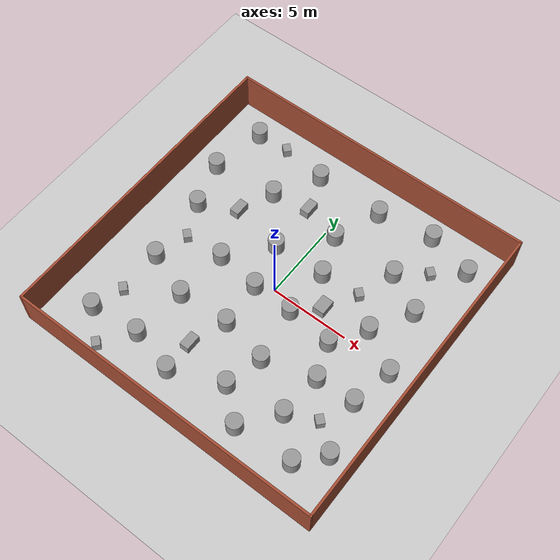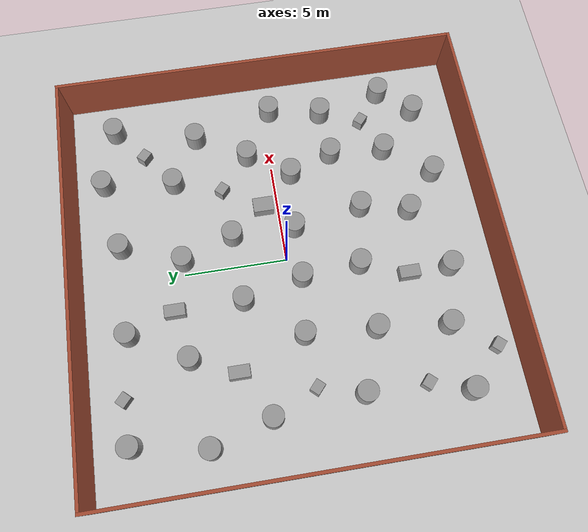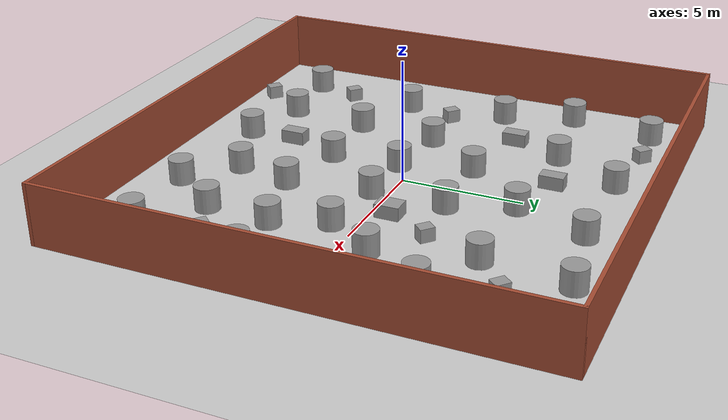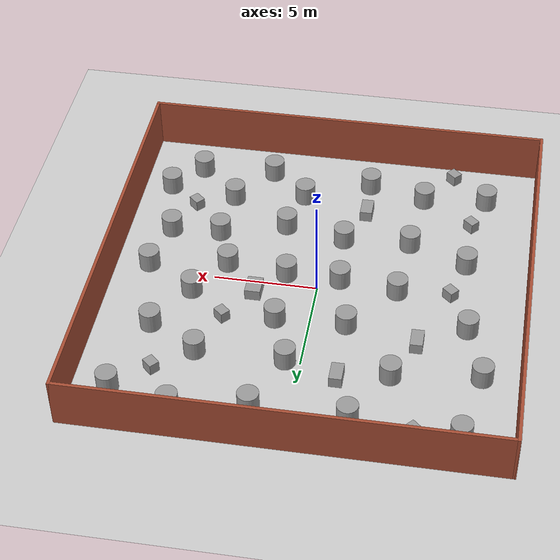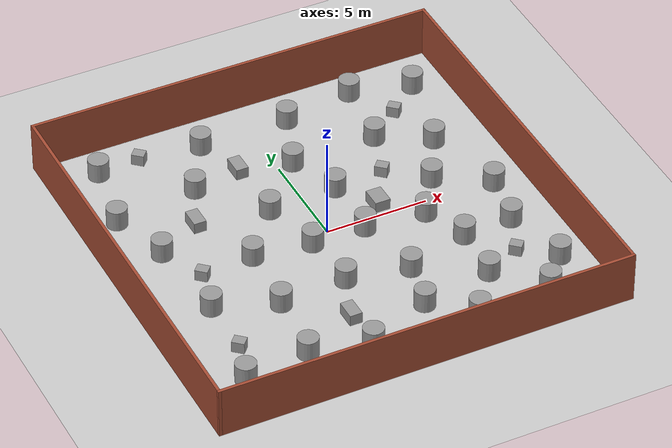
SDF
<sdf version="1.7">
 <world name="default">
  <light name="sun" type="directional">
   <pose>0 0 10 0 -0 0</pose>
   <diffuse>0.8 0.8 0.8 1</diffuse>
   <specular>0.2 0.2 0.2 1</specular>
   <attenuation>
    <range>1000</range>
    <constant>0.9</constant>
    <linear>0.01</linear>
    <quadratic>0.001</quadratic>
   </attenuation>
   <direction>-0.5 0.1 -0.9</direction>
   <spot><inner_angle>0</inner_angle><outer_angle>0</outer_angle><falloff>0</falloff></spot>
  </light>
  <model name="ground_plane">
   <static>1</static>
   <link name="link">
    <collision name="collision">
     <geometry><plane><normal>0 0 1</normal><size>100 100</size></plane></geometry>
     <surface><friction><ode><mu>100</mu><mu2>50</mu2></ode></friction></surface>
    </collision>
    <visual name="visual">
     <cast_shadows>0</cast_shadows>
     <geometry><plane><normal>0 0 1</normal><size>100 100</size></plane></geometry>
     <material>
      <script><uri>file://media/materials/scripts/gazebo.material</uri><name>Gazebo/Grey</name></script>
     </material>
    </visual>
   </link>
  </model>
  <gravity>0 0 -9.8</gravity>
  <magnetic_field>6e-06 2.3e-05 -4.2e-05</magnetic_field>
  <atmosphere type="adiabatic"/>
  <physics type="ode">
   <max_step_size>0.01</max_step_size>
   <real_time_factor>1</real_time_factor>
   <real_time_update_rate>1000</real_time_update_rate>
  </physics>
  <scene><ambient>0.4 0.4 0.4 1</ambient><background>0.7 0.7 0.7 1</background><shadows>1</shadows></scene>
  <spherical_coordinates>
   <surface_model>EARTH_WGS84</surface_model>
   <latitude_deg>0</latitude_deg>
   <longitude_deg>0</longitude_deg>
   <elevation>0</elevation>
   <heading_deg>0</heading_deg>
  </spherical_coordinates>
  <model name="20_20_wall">
   <link name="Wall_0">
    <collision name="Wall_0_Collision">
     <geometry><box><size>20.15 0.15 2.5</size></box></geometry>
     <pose>0 0 1.25 0 -0 0</pose>
    </collision>
    <visual name="Wall_0_Visual">
     <pose>0 0 1.25 0 -0 0</pose>
     <geometry><box><size>20.15 0.15 2.5</size></box></geometry>
     <material>
      <script><uri>file://media/materials/scripts/gazebo.material</uri><name>Gazebo/Bricks</name></script>
      <ambient>1 1 1 1</ambient>
     </material>
     <meta><layer>0</layer></meta>
    </visual>
    <pose>0 10 0 0 -0 0</pose>
   </link>
   <link name="Wall_1">
    <collision name="Wall_1_Collision">
     <geometry><box><size>20.15 0.15 2.5</size></box></geometry>
     <pose>0 0 1.25 0 -0 0</pose>
    </collision>
    <visual name="Wall_1_Visual">
     <pose>0 0 1.25 0 -0 0</pose>
     <geometry><box><size>20.15 0.15 2.5</size></box></geometry>
     <material>
      <script><uri>file://media/materials/scripts/gazebo.material</uri><name>Gazebo/Bricks</name></script>
      <ambient>1 1 1 1</ambient>
     </material>
     <meta><layer>0</layer></meta>
    </visual>
    <pose>10 0 0 0 -0 -1.5708</pose>
   </link>
   <link name="Wall_2">
    <collision name="Wall_2_Collision">
     <geometry><box><size>20.15 0.15 2.5</size></box></geometry>
     <pose>0 0 1.25 0 -0 0</pose>
    </collision>
    <visual name="Wall_2_Visual">
     <pose>0 0 1.25 0 -0 0</pose>
     <geometry><box><size>20.15 0.15 2.5</size></box></geometry>
     <material>
      <script><uri>file://media/materials/scripts/gazebo.material</uri><name>Gazebo/Bricks</name></script>
      <ambient>1 1 1 1</ambient>
     </material>
     <meta><layer>0</layer></meta>
    </visual>
    <pose>0 -10 0 0 -0 3.14159</pose>
   </link>
   <link name="Wall_3">
    <collision name="Wall_3_Collision">
     <geometry><box><size>20.15 0.15 2.5</size></box></geometry>
     <pose>0 0 1.25 0 -0 0</pose>
    </collision>
    <visual name="Wall_3_Visual">
     <pose>0 0 1.25 0 -0 0</pose>
     <geometry><box><size>20.15 0.15 2.5</size></box></geometry>
     <material>
      <script><uri>file://media/materials/scripts/gazebo.material</uri><name>Gazebo/Bricks</name></script>
      <ambient>1 1 1 1</ambient>
     </material>
     <meta><layer>0</layer></meta>
    </visual>
    <pose>-10 0 0 0 -0 1.5708</pose>
   </link>
   <static>1</static>
  </model>
  <model name="固定圆柱">
   <link name="link">
    <inertial>
     <mass>1</mass>
     <inertia><ixx>0.145833</ixx><ixy>0</ixy><ixz>0</ixz><iyy>0.145833</iyy><iyz>0</iyz><izz>0.125</izz></inertia>
    </inertial>
    <visual name="visual">
     <geometry><cylinder><radius>0.5</radius><length>1</length></cylinder></geometry>
     <material>
      <script><name>Gazebo/Grey</name><uri>file://media/materials/scripts/gazebo.material</uri></script>
      <shader type="pixel"><normal_map>__default__</normal_map></shader>
     </material>
    </visual>
    <collision name="collision">
     <geometry><cylinder><radius>0.5</radius><length>1</length></cylinder></geometry>
     <surface>
      <friction>
       <ode><mu>1</mu><mu2>1</mu2><fdir1>0 0 0</fdir1><slip1>0</slip1><slip2>0</slip2></ode>
       <torsional>
        <coefficient>1</coefficient>
        <patch_radius>0</patch_radius>
        <surface_radius>0</surface_radius>
        <use_patch_radius>1</use_patch_radius>
        <ode><slip>0</slip></ode>
       </torsional>
      </friction>
      <bounce><restitution_coefficient>0</restitution_coefficient><threshold>1e+06</threshold></bounce>
      <contact>
       <collide_without_contact>0</collide_without_contact>
       <collide_without_contact_bitmask>1</collide_without_contact_bitmask>
       <collide_bitmask>1</collide_bitmask>
       <ode>
        <soft_cfm>0</soft_cfm>
        <soft_erp>0.2</soft_erp>
        <kp>1e+13</kp>
        <kd>1</kd>
        <max_vel>0.01</max_vel>
        <min_depth>0</min_depth>
       </ode>
       <bullet>
        <split_impulse>1</split_impulse>
        <split_impulse_penetration_threshold>-0.01</split_impulse_penetration_threshold>
        <soft_cfm>0</soft_cfm>
        <soft_erp>0.2</soft_erp>
        <kp>1e+13</kp>
        <kd>1</kd>
       </bullet>
      </contact>
     </surface>
    </collision>
   </link>
   <static>1</static>
   <pose>0.688811 4.97248 0.5 0 -0 0</pose>
  </model>
  <model name="固定圆柱_clone">
   <link name="link">
    <inertial>
     <mass>1</mass>
     <inertia><ixx>0.145833</ixx><ixy>0</ixy><ixz>0</ixz><iyy>0.145833</iyy><iyz>0</iyz><izz>0.125</izz></inertia>
    </inertial>
    <visual name="visual">
     <geometry><cylinder><radius>0.5</radius><length>1</length></cylinder></geometry>
     <material>
      <script><name>Gazebo/Grey</name><uri>file://media/materials/scripts/gazebo.material</uri></script>
      <shader type="pixel"><normal_map>__default__</normal_map></shader>
     </material>
    </visual>
    <collision name="collision">
     <geometry><cylinder><radius>0.5</radius><length>1</length></cylinder></geometry>
     <surface>
      <friction>
       <ode><mu>1</mu><mu2>1</mu2><fdir1>0 0 0</fdir1><slip1>0</slip1><slip2>0</slip2></ode>
       <torsional>
        <coefficient>1</coefficient>
        <patch_radius>0</patch_radius>
        <surface_radius>0</surface_radius>
        <use_patch_radius>1</use_patch_radius>
        <ode><slip>0</slip></ode>
       </torsional>
      </friction>
      <bounce><restitution_coefficient>0</restitution_coefficient><threshold>1e+06</threshold></bounce>
      <contact>
       <collide_without_contact>0</collide_without_contact>
       <collide_without_contact_bitmask>1</collide_without_contact_bitmask>
       <collide_bitmask>1</collide_bitmask>
       <ode>
        <soft_cfm>0</soft_cfm>
        <soft_erp>0.2</soft_erp>
        <kp>1e+13</kp>
        <kd>1</kd>
        <max_vel>0.01</max_vel>
        <min_depth>0</min_depth>
       </ode>
       <bullet>
        <split_impulse>1</split_impulse>
        <split_impulse_penetration_threshold>-0.01</split_impulse_penetration_threshold>
        <soft_cfm>0</soft_cfm>
        <soft_erp>0.2</soft_erp>
        <kp>1e+13</kp>
        <kd>1</kd>
       </bullet>
      </contact>
     </surface>
    </collision>
   </link>
   <static>1</static>
   <pose>-4.14469 5.18074 0.5 0 -0 0</pose>
  </model>
  <model name="固定圆柱_clone_0">
   <link name="link">
    <inertial>
     <mass>1</mass>
     <inertia><ixx>0.145833</ixx><ixy>0</ixy><ixz>0</ixz><iyy>0.145833</iyy><iyz>0</iyz><izz>0.125</izz></inertia>
    </inertial>
    <visual name="visual">
     <geometry><cylinder><radius>0.5</radius><length>1</length></cylinder></geometry>
     <material>
      <script><name>Gazebo/Grey</name><uri>file://media/materials/scripts/gazebo.material</uri></script>
      <shader type="pixel"><normal_map>__default__</normal_map></shader>
     </material>
    </visual>
    <collision name="collision">
     <geometry><cylinder><radius>0.5</radius><length>1</length></cylinder></geometry>
     <surface>
      <friction>
       <ode><mu>1</mu><mu2>1</mu2><fdir1>0 0 0</fdir1><slip1>0</slip1><slip2>0</slip2></ode>
       <torsional>
        <coefficient>1</coefficient>
        <patch_radius>0</patch_radius>
        <surface_radius>0</surface_radius>
        <use_patch_radius>1</use_patch_radius>
        <ode><slip>0</slip></ode>
       </torsional>
      </friction>
      <bounce><restitution_coefficient>0</restitution_coefficient><threshold>1e+06</threshold></bounce>
      <contact>
       <collide_without_contact>0</collide_without_contact>
       <collide_without_contact_bitmask>1</collide_without_contact_bitmask>
       <collide_bitmask>1</collide_bitmask>
       <ode>
        <soft_cfm>0</soft_cfm>
        <soft_erp>0.2</soft_erp>
        <kp>1e+13</kp>
        <kd>1</kd>
        <max_vel>0.01</max_vel>
        <min_depth>0</min_depth>
       </ode>
       <bullet>
        <split_impulse>1</split_impulse>
        <split_impulse_penetration_threshold>-0.01</split_impulse_penetration_threshold>
        <soft_cfm>0</soft_cfm>
        <soft_erp>0.2</soft_erp>
        <kp>1e+13</kp>
        <kd>1</kd>
       </bullet>
      </contact>
     </surface>
    </collision>
   </link>
   <static>1</static>
   <pose>-0.799824 -3.4541 0.5 0 -0 0</pose>
  </model>
  <model name="固定圆柱_clone_1">
   <link name="link">
    <inertial>
     <mass>1</mass>
     <inertia><ixx>0.145833</ixx><ixy>0</ixy><ixz>0</ixz><iyy>0.145833</iyy><iyz>0</iyz><izz>0.125</izz></inertia>
    </inertial>
    <visual name="visual">
     <geometry><cylinder><radius>0.5</radius><length>1</length></cylinder></geometry>
     <material>
      <script><name>Gazebo/Grey</name><uri>file://media/materials/scripts/gazebo.material</uri></script>
      <shader type="pixel"><normal_map>__default__</normal_map></shader>
     </material>
    </visual>
    <collision name="collision">
     <geometry><cylinder><radius>0.5</radius><length>1</length></cylinder></geometry>
     <surface>
      <friction>
       <ode><mu>1</mu><mu2>1</mu2><fdir1>0 0 0</fdir1><slip1>0</slip1><slip2>0</slip2></ode>
       <torsional>
        <coefficient>1</coefficient>
        <patch_radius>0</patch_radius>
        <surface_radius>0</surface_radius>
        <use_patch_radius>1</use_patch_radius>
        <ode><slip>0</slip></ode>
       </torsional>
      </friction>
      <bounce><restitution_coefficient>0</restitution_coefficient><threshold>1e+06</threshold></bounce>
      <contact>
       <collide_without_contact>0</collide_without_contact>
       <collide_without_contact_bitmask>1</collide_without_contact_bitmask>
       <collide_bitmask>1</collide_bitmask>
       <ode>
        <soft_cfm>0</soft_cfm>
        <soft_erp>0.2</soft_erp>
        <kp>1e+13</kp>
        <kd>1</kd>
        <max_vel>0.01</max_vel>
        <min_depth>0</min_depth>
       </ode>
       <bullet>
        <split_impulse>1</split_impulse>
        <split_impulse_penetration_threshold>-0.01</split_impulse_penetration_threshold>
        <soft_cfm>0</soft_cfm>
        <soft_erp>0.2</soft_erp>
        <kp>1e+13</kp>
        <kd>1</kd>
       </bullet>
      </contact>
     </surface>
    </collision>
   </link>
   <static>1</static>
   <pose>-3.82318 -0.245467 0.5 0 -0 0</pose>
  </model>
  <model name="固定圆柱_clone_2">
   <link name="link">
    <inertial>
     <mass>1</mass>
     <inertia><ixx>0.145833</ixx><ixy>0</ixy><ixz>0</ixz><iyy>0.145833</iyy><iyz>0</iyz><izz>0.125</izz></inertia>
    </inertial>
    <visual name="visual">
     <geometry><cylinder><radius>0.5</radius><length>1</length></cylinder></geometry>
     <material>
      <script><name>Gazebo/Grey</name><uri>file://media/materials/scripts/gazebo.material</uri></script>
      <shader type="pixel"><normal_map>__default__</normal_map></shader>
     </material>
    </visual>
    <collision name="collision">
     <geometry><cylinder><radius>0.5</radius><length>1</length></cylinder></geometry>
     <surface>
      <friction>
       <ode><mu>1</mu><mu2>1</mu2><fdir1>0 0 0</fdir1><slip1>0</slip1><slip2>0</slip2></ode>
       <torsional>
        <coefficient>1</coefficient>
        <patch_radius>0</patch_radius>
        <surface_radius>0</surface_radius>
        <use_patch_radius>1</use_patch_radius>
        <ode><slip>0</slip></ode>
       </torsional>
      </friction>
      <bounce><restitution_coefficient>0</restitution_coefficient><threshold>1e+06</threshold></bounce>
      <contact>
       <collide_without_contact>0</collide_without_contact>
       <collide_without_contact_bitmask>1</collide_without_contact_bitmask>
       <collide_bitmask>1</collide_bitmask>
       <ode>
        <soft_cfm>0</soft_cfm>
        <soft_erp>0.2</soft_erp>
        <kp>1e+13</kp>
        <kd>1</kd>
        <max_vel>0.01</max_vel>
        <min_depth>0</min_depth>
       </ode>
       <bullet>
        <split_impulse>1</split_impulse>
        <split_impulse_penetration_threshold>-0.01</split_impulse_penetration_threshold>
        <soft_cfm>0</soft_cfm>
        <soft_erp>0.2</soft_erp>
        <kp>1e+13</kp>
        <kd>1</kd>
       </bullet>
      </contact>
     </surface>
    </collision>
   </link>
   <static>1</static>
   <pose>1.58502 -0.63716 0.5 0 -0 0</pose>
  </model>
  <model name="固定圆柱_clone_3">
   <link name="link">
    <inertial>
     <mass>1</mass>
     <inertia><ixx>0.145833</ixx><ixy>0</ixy><ixz>0</ixz><iyy>0.145833</iyy><iyz>0</iyz><izz>0.125</izz></inertia>
    </inertial>
    <visual name="visual">
     <geometry><cylinder><radius>0.5</radius><length>1</length></cylinder></geometry>
     <material>
      <script><name>Gazebo/Grey</name><uri>file://media/materials/scripts/gazebo.material</uri></script>
      <shader type="pixel"><normal_map>__default__</normal_map></shader>
     </material>
    </visual>
    <collision name="collision">
     <geometry><cylinder><radius>0.5</radius><length>1</length></cylinder></geometry>
     <surface>
      <friction>
       <ode><mu>1</mu><mu2>1</mu2><fdir1>0 0 0</fdir1><slip1>0</slip1><slip2>0</slip2></ode>
       <torsional>
        <coefficient>1</coefficient>
        <patch_radius>0</patch_radius>
        <surface_radius>0</surface_radius>
        <use_patch_radius>1</use_patch_radius>
        <ode><slip>0</slip></ode>
       </torsional>
      </friction>
      <bounce><restitution_coefficient>0</restitution_coefficient><threshold>1e+06</threshold></bounce>
      <contact>
       <collide_without_contact>0</collide_without_contact>
       <collide_without_contact_bitmask>1</collide_without_contact_bitmask>
       <collide_bitmask>1</collide_bitmask>
       <ode>
        <soft_cfm>0</soft_cfm>
        <soft_erp>0.2</soft_erp>
        <kp>1e+13</kp>
        <kd>1</kd>
        <max_vel>0.01</max_vel>
        <min_depth>0</min_depth>
       </ode>
       <bullet>
        <split_impulse>1</split_impulse>
        <split_impulse_penetration_threshold>-0.01</split_impulse_penetration_threshold>
        <soft_cfm>0</soft_cfm>
        <soft_erp>0.2</soft_erp>
        <kp>1e+13</kp>
        <kd>1</kd>
       </bullet>
      </contact>
     </surface>
    </collision>
   </link>
   <static>1</static>
   <pose>4.88498 4.9968 0.5 0 -0 0</pose>
  </model>
  <model name="固定圆柱_clone_4">
   <link name="link">
    <inertial>
     <mass>1</mass>
     <inertia><ixx>0.145833</ixx><ixy>0</ixy><ixz>0</ixz><iyy>0.145833</iyy><iyz>0</iyz><izz>0.125</izz></inertia>
    </inertial>
    <visual name="visual">
     <geometry><cylinder><radius>0.5</radius><length>1</length></cylinder></geometry>
     <material>
      <script><name>Gazebo/Grey</name><uri>file://media/materials/scripts/gazebo.material</uri></script>
      <shader type="pixel"><normal_map>__default__</normal_map></shader>
     </material>
    </visual>
    <collision name="collision">
     <geometry><cylinder><radius>0.5</radius><length>1</length></cylinder></geometry>
     <surface>
      <friction>
       <ode><mu>1</mu><mu2>1</mu2><fdir1>0 0 0</fdir1><slip1>0</slip1><slip2>0</slip2></ode>
       <torsional>
        <coefficient>1</coefficient>
        <patch_radius>0</patch_radius>
        <surface_radius>0</surface_radius>
        <use_patch_radius>1</use_patch_radius>
        <ode><slip>0</slip></ode>
       </torsional>
      </friction>
      <bounce><restitution_coefficient>0</restitution_coefficient><threshold>1e+06</threshold></bounce>
      <contact>
       <collide_without_contact>0</collide_without_contact>
       <collide_without_contact_bitmask>1</collide_without_contact_bitmask>
       <collide_bitmask>1</collide_bitmask>
       <ode>
        <soft_cfm>0</soft_cfm>
        <soft_erp>0.2</soft_erp>
        <kp>1e+13</kp>
        <kd>1</kd>
        <max_vel>0.01</max_vel>
        <min_depth>0</min_depth>
       </ode>
       <bullet>
        <split_impulse>1</split_impulse>
        <split_impulse_penetration_threshold>-0.01</split_impulse_penetration_threshold>
        <soft_cfm>0</soft_cfm>
        <soft_erp>0.2</soft_erp>
        <kp>1e+13</kp>
        <kd>1</kd>
       </bullet>
      </contact>
     </surface>
    </collision>
   </link>
   <static>1</static>
   <pose>5.13074 -5.82469 0.5 0 -0 0</pose>
  </model>
  <model name="固定圆柱_clone_5">
   <link name="link">
    <inertial>
     <mass>1</mass>
     <inertia><ixx>0.145833</ixx><ixy>0</ixy><ixz>0</ixz><iyy>0.145833</iyy><iyz>0</iyz><izz>0.125</izz></inertia>
    </inertial>
    <visual name="visual">
     <geometry><cylinder><radius>0.5</radius><length>1</length></cylinder></geometry>
     <material>
      <script><name>Gazebo/Grey</name><uri>file://media/materials/scripts/gazebo.material</uri></script>
      <shader type="pixel"><normal_map>__default__</normal_map></shader>
     </material>
    </visual>
    <collision name="collision">
     <geometry><cylinder><radius>0.5</radius><length>1</length></cylinder></geometry>
     <surface>
      <friction>
       <ode><mu>1</mu><mu2>1</mu2><fdir1>0 0 0</fdir1><slip1>0</slip1><slip2>0</slip2></ode>
       <torsional>
        <coefficient>1</coefficient>
        <patch_radius>0</patch_radius>
        <surface_radius>0</surface_radius>
        <use_patch_radius>1</use_patch_radius>
        <ode><slip>0</slip></ode>
       </torsional>
      </friction>
      <bounce><restitution_coefficient>0</restitution_coefficient><threshold>1e+06</threshold></bounce>
      <contact>
       <collide_without_contact>0</collide_without_contact>
       <collide_without_contact_bitmask>1</collide_without_contact_bitmask>
       <collide_bitmask>1</collide_bitmask>
       <ode>
        <soft_cfm>0</soft_cfm>
        <soft_erp>0.2</soft_erp>
        <kp>1e+13</kp>
        <kd>1</kd>
        <max_vel>0.01</max_vel>
        <min_depth>0</min_depth>
       </ode>
       <bullet>
        <split_impulse>1</split_impulse>
        <split_impulse_penetration_threshold>-0.01</split_impulse_penetration_threshold>
        <soft_cfm>0</soft_cfm>
        <soft_erp>0.2</soft_erp>
        <kp>1e+13</kp>
        <kd>1</kd>
       </bullet>
      </contact>
     </surface>
    </collision>
   </link>
   <static>1</static>
   <pose>1.6118 -6.41611 0.5 0 -0 0</pose>
  </model>
  <model name="固定圆柱_clone_6">
   <link name="link">
    <inertial>
     <mass>1</mass>
     <inertia><ixx>0.145833</ixx><ixy>0</ixy><ixz>0</ixz><iyy>0.145833</iyy><iyz>0</iyz><izz>0.125</izz></inertia>
    </inertial>
    <visual name="visual">
     <geometry><cylinder><radius>0.5</radius><length>1</length></cylinder></geometry>
     <material>
      <script><name>Gazebo/Grey</name><uri>file://media/materials/scripts/gazebo.material</uri></script>
      <shader type="pixel"><normal_map>__default__</normal_map></shader>
     </material>
    </visual>
    <collision name="collision">
     <geometry><cylinder><radius>0.5</radius><length>1</length></cylinder></geometry>
     <surface>
      <friction>
       <ode><mu>1</mu><mu2>1</mu2><fdir1>0 0 0</fdir1><slip1>0</slip1><slip2>0</slip2></ode>
       <torsional>
        <coefficient>1</coefficient>
        <patch_radius>0</patch_radius>
        <surface_radius>0</surface_radius>
        <use_patch_radius>1</use_patch_radius>
        <ode><slip>0</slip></ode>
       </torsional>
      </friction>
      <bounce><restitution_coefficient>0</restitution_coefficient><threshold>1e+06</threshold></bounce>
      <contact>
       <collide_without_contact>0</collide_without_contact>
       <collide_without_contact_bitmask>1</collide_without_contact_bitmask>
       <collide_bitmask>1</collide_bitmask>
       <ode>
        <soft_cfm>0</soft_cfm>
        <soft_erp>0.2</soft_erp>
        <kp>1e+13</kp>
        <kd>1</kd>
        <max_vel>0.01</max_vel>
        <min_depth>0</min_depth>
       </ode>
       <bullet>
        <split_impulse>1</split_impulse>
        <split_impulse_penetration_threshold>-0.01</split_impulse_penetration_threshold>
        <soft_cfm>0</soft_cfm>
        <soft_erp>0.2</soft_erp>
        <kp>1e+13</kp>
        <kd>1</kd>
       </bullet>
      </contact>
     </surface>
    </collision>
   </link>
   <static>1</static>
   <pose>5.86042 1.12448 0.5 0 -0 0</pose>
  </model>
  <model name="固定圆柱_clone_7">
   <link name="link">
    <inertial>
     <mass>1</mass>
     <inertia><ixx>0.145833</ixx><ixy>0</ixy><ixz>0</ixz><iyy>0.145833</iyy><iyz>0</iyz><izz>0.125</izz></inertia>
    </inertial>
    <visual name="visual">
     <geometry><cylinder><radius>0.5</radius><length>1</length></cylinder></geometry>
     <material>
      <script><name>Gazebo/Grey</name><uri>file://media/materials/scripts/gazebo.material</uri></script>
      <shader type="pixel"><normal_map>__default__</normal_map></shader>
     </material>
    </visual>
    <collision name="collision">
     <geometry><cylinder><radius>0.5</radius><length>1</length></cylinder></geometry>
     <surface>
      <friction>
       <ode><mu>1</mu><mu2>1</mu2><fdir1>0 0 0</fdir1><slip1>0</slip1><slip2>0</slip2></ode>
       <torsional>
        <coefficient>1</coefficient>
        <patch_radius>0</patch_radius>
        <surface_radius>0</surface_radius>
        <use_patch_radius>1</use_patch_radius>
        <ode><slip>0</slip></ode>
       </torsional>
      </friction>
      <bounce><restitution_coefficient>0</restitution_coefficient><threshold>1e+06</threshold></bounce>
      <contact>
       <collide_without_contact>0</collide_without_contact>
       <collide_without_contact_bitmask>1</collide_without_contact_bitmask>
       <collide_bitmask>1</collide_bitmask>
       <ode>
        <soft_cfm>0</soft_cfm>
        <soft_erp>0.2</soft_erp>
        <kp>1e+13</kp>
        <kd>1</kd>
        <max_vel>0.01</max_vel>
        <min_depth>0</min_depth>
       </ode>
       <bullet>
        <split_impulse>1</split_impulse>
        <split_impulse_penetration_threshold>-0.01</split_impulse_penetration_threshold>
        <soft_cfm>0</soft_cfm>
        <soft_erp>0.2</soft_erp>
        <kp>1e+13</kp>
        <kd>1</kd>
       </bullet>
      </contact>
     </surface>
    </collision>
   </link>
   <static>1</static>
   <pose>8.25202 7.7046 0.5 0 -0 0</pose>
  </model>
  <model name="固定圆柱_clone_8">
   <link name="link">
    <inertial>
     <mass>1</mass>
     <inertia><ixx>0.145833</ixx><ixy>0</ixy><ixz>0</ixz><iyy>0.145833</iyy><iyz>0</iyz><izz>0.125</izz></inertia>
    </inertial>
    <visual name="visual">
     <geometry><cylinder><radius>0.5</radius><length>1</length></cylinder></geometry>
     <material>
      <script><name>Gazebo/Grey</name><uri>file://media/materials/scripts/gazebo.material</uri></script>
      <shader type="pixel"><normal_map>__default__</normal_map></shader>
     </material>
    </visual>
    <collision name="collision">
     <geometry><cylinder><radius>0.5</radius><length>1</length></cylinder></geometry>
     <surface>
      <friction>
       <ode><mu>1</mu><mu2>1</mu2><fdir1>0 0 0</fdir1><slip1>0</slip1><slip2>0</slip2></ode>
       <torsional>
        <coefficient>1</coefficient>
        <patch_radius>0</patch_radius>
        <surface_radius>0</surface_radius>
        <use_patch_radius>1</use_patch_radius>
        <ode><slip>0</slip></ode>
       </torsional>
      </friction>
      <bounce><restitution_coefficient>0</restitution_coefficient><threshold>1e+06</threshold></bounce>
      <contact>
       <collide_without_contact>0</collide_without_contact>
       <collide_without_contact_bitmask>1</collide_without_contact_bitmask>
       <collide_bitmask>1</collide_bitmask>
       <ode>
        <soft_cfm>0</soft_cfm>
        <soft_erp>0.2</soft_erp>
        <kp>1e+13</kp>
        <kd>1</kd>
        <max_vel>0.01</max_vel>
        <min_depth>0</min_depth>
       </ode>
       <bullet>
        <split_impulse>1</split_impulse>
        <split_impulse_penetration_threshold>-0.01</split_impulse_penetration_threshold>
        <soft_cfm>0</soft_cfm>
        <soft_erp>0.2</soft_erp>
        <kp>1e+13</kp>
        <kd>1</kd>
       </bullet>
      </contact>
     </surface>
    </collision>
   </link>
   <static>1</static>
   <pose>1.81026 7.9231 0.5 0 -0 0</pose>
  </model>
  <model name="固定圆柱_clone_9">
   <link name="link">
    <inertial>
     <mass>1</mass>
     <inertia><ixx>0.145833</ixx><ixy>0</ixy><ixz>0</ixz><iyy>0.145833</iyy><iyz>0</iyz><izz>0.125</izz></inertia>
    </inertial>
    <visual name="visual">
     <geometry><cylinder><radius>0.5</radius><length>1</length></cylinder></geometry>
     <material>
      <script><name>Gazebo/Grey</name><uri>file://media/materials/scripts/gazebo.material</uri></script>
      <shader type="pixel"><normal_map>__default__</normal_map></shader>
     </material>
    </visual>
    <collision name="collision">
     <geometry><cylinder><radius>0.5</radius><length>1</length></cylinder></geometry>
     <surface>
      <friction>
       <ode><mu>1</mu><mu2>1</mu2><fdir1>0 0 0</fdir1><slip1>0</slip1><slip2>0</slip2></ode>
       <torsional>
        <coefficient>1</coefficient>
        <patch_radius>0</patch_radius>
        <surface_radius>0</surface_radius>
        <use_patch_radius>1</use_patch_radius>
        <ode><slip>0</slip></ode>
       </torsional>
      </friction>
      <bounce><restitution_coefficient>0</restitution_coefficient><threshold>1e+06</threshold></bounce>
      <contact>
       <collide_without_contact>0</collide_without_contact>
       <collide_without_contact_bitmask>1</collide_without_contact_bitmask>
       <collide_bitmask>1</collide_bitmask>
       <ode>
        <soft_cfm>0</soft_cfm>
        <soft_erp>0.2</soft_erp>
        <kp>1e+13</kp>
        <kd>1</kd>
        <max_vel>0.01</max_vel>
        <min_depth>0</min_depth>
       </ode>
       <bullet>
        <split_impulse>1</split_impulse>
        <split_impulse_penetration_threshold>-0.01</split_impulse_penetration_threshold>
        <soft_cfm>0</soft_cfm>
        <soft_erp>0.2</soft_erp>
        <kp>1e+13</kp>
        <kd>1</kd>
       </bullet>
      </contact>
     </surface>
    </collision>
   </link>
   <static>1</static>
   <pose>-2.59298 7.92968 0.5 0 -0 0</pose>
  </model>
  <model name="固定圆柱_clone_10">
   <link name="link">
    <inertial>
     <mass>1</mass>
     <inertia><ixx>0.145833</ixx><ixy>0</ixy><ixz>0</ixz><iyy>0.145833</iyy><iyz>0</iyz><izz>0.125</izz></inertia>
    </inertial>
    <visual name="visual">
     <geometry><cylinder><radius>0.5</radius><length>1</length></cylinder></geometry>
     <material>
      <script><name>Gazebo/Grey</name><uri>file://media/materials/scripts/gazebo.material</uri></script>
      <shader type="pixel"><normal_map>__default__</normal_map></shader>
     </material>
    </visual>
    <collision name="collision">
     <geometry><cylinder><radius>0.5</radius><length>1</length></cylinder></geometry>
     <surface>
      <friction>
       <ode><mu>1</mu><mu2>1</mu2><fdir1>0 0 0</fdir1><slip1>0</slip1><slip2>0</slip2></ode>
       <torsional>
        <coefficient>1</coefficient>
        <patch_radius>0</patch_radius>
        <surface_radius>0</surface_radius>
        <use_patch_radius>1</use_patch_radius>
        <ode><slip>0</slip></ode>
       </torsional>
      </friction>
      <bounce><restitution_coefficient>0</restitution_coefficient><threshold>1e+06</threshold></bounce>
      <contact>
       <collide_without_contact>0</collide_without_contact>
       <collide_without_contact_bitmask>1</collide_without_contact_bitmask>
       <collide_bitmask>1</collide_bitmask>
       <ode>
        <soft_cfm>0</soft_cfm>
        <soft_erp>0.2</soft_erp>
        <kp>1e+13</kp>
        <kd>1</kd>
        <max_vel>0.01</max_vel>
        <min_depth>0</min_depth>
       </ode>
       <bullet>
        <split_impulse>1</split_impulse>
        <split_impulse_penetration_threshold>-0.01</split_impulse_penetration_threshold>
        <soft_cfm>0</soft_cfm>
        <soft_erp>0.2</soft_erp>
        <kp>1e+13</kp>
        <kd>1</kd>
       </bullet>
      </contact>
     </surface>
    </collision>
   </link>
   <static>1</static>
   <pose>-7.60473 8.21031 0.5 0 -0 0</pose>
  </model>
  <model name="固定圆柱_clone_11">
   <link name="link">
    <inertial>
     <mass>1</mass>
     <inertia><ixx>0.145833</ixx><ixy>0</ixy><ixz>0</ixz><iyy>0.145833</iyy><iyz>0</iyz><izz>0.125</izz></inertia>
    </inertial>
    <visual name="visual">
     <geometry><cylinder><radius>0.5</radius><length>1</length></cylinder></geometry>
     <material>
      <script><name>Gazebo/Grey</name><uri>file://media/materials/scripts/gazebo.material</uri></script>
      <shader type="pixel"><normal_map>__default__</normal_map></shader>
     </material>
    </visual>
    <collision name="collision">
     <geometry><cylinder><radius>0.5</radius><length>1</length></cylinder></geometry>
     <surface>
      <friction>
       <ode><mu>1</mu><mu2>1</mu2><fdir1>0 0 0</fdir1><slip1>0</slip1><slip2>0</slip2></ode>
       <torsional>
        <coefficient>1</coefficient>
        <patch_radius>0</patch_radius>
        <surface_radius>0</surface_radius>
        <use_patch_radius>1</use_patch_radius>
        <ode><slip>0</slip></ode>
       </torsional>
      </friction>
      <bounce><restitution_coefficient>0</restitution_coefficient><threshold>1e+06</threshold></bounce>
      <contact>
       <collide_without_contact>0</collide_without_contact>
       <collide_without_contact_bitmask>1</collide_without_contact_bitmask>
       <collide_bitmask>1</collide_bitmask>
       <ode>
        <soft_cfm>0</soft_cfm>
        <soft_erp>0.2</soft_erp>
        <kp>1e+13</kp>
        <kd>1</kd>
        <max_vel>0.01</max_vel>
        <min_depth>0</min_depth>
       </ode>
       <bullet>
        <split_impulse>1</split_impulse>
        <split_impulse_penetration_threshold>-0.01</split_impulse_penetration_threshold>
        <soft_cfm>0</soft_cfm>
        <soft_erp>0.2</soft_erp>
        <kp>1e+13</kp>
        <kd>1</kd>
       </bullet>
      </contact>
     </surface>
    </collision>
   </link>
   <static>1</static>
   <pose>-6.92949 -2.5396 0.5 0 -0 0</pose>
  </model>
  <model name="固定圆柱_clone_12">
   <link name="link">
    <inertial>
     <mass>1</mass>
     <inertia><ixx>0.145833</ixx><ixy>0</ixy><ixz>0</ixz><iyy>0.145833</iyy><iyz>0</iyz><izz>0.125</izz></inertia>
    </inertial>
    <visual name="visual">
     <geometry><cylinder><radius>0.5</radius><length>1</length></cylinder></geometry>
     <material>
      <script><name>Gazebo/Grey</name><uri>file://media/materials/scripts/gazebo.material</uri></script>
      <shader type="pixel"><normal_map>__default__</normal_map></shader>
     </material>
    </visual>
    <collision name="collision">
     <geometry><cylinder><radius>0.5</radius><length>1</length></cylinder></geometry>
     <surface>
      <friction>
       <ode><mu>1</mu><mu2>1</mu2><fdir1>0 0 0</fdir1><slip1>0</slip1><slip2>0</slip2></ode>
       <torsional>
        <coefficient>1</coefficient>
        <patch_radius>0</patch_radius>
        <surface_radius>0</surface_radius>
        <use_patch_radius>1</use_patch_radius>
        <ode><slip>0</slip></ode>
       </torsional>
      </friction>
      <bounce><restitution_coefficient>0</restitution_coefficient><threshold>1e+06</threshold></bounce>
      <contact>
       <collide_without_contact>0</collide_without_contact>
       <collide_without_contact_bitmask>1</collide_without_contact_bitmask>
       <collide_bitmask>1</collide_bitmask>
       <ode>
        <soft_cfm>0</soft_cfm>
        <soft_erp>0.2</soft_erp>
        <kp>1e+13</kp>
        <kd>1</kd>
        <max_vel>0.01</max_vel>
        <min_depth>0</min_depth>
       </ode>
       <bullet>
        <split_impulse>1</split_impulse>
        <split_impulse_penetration_threshold>-0.01</split_impulse_penetration_threshold>
        <soft_cfm>0</soft_cfm>
        <soft_erp>0.2</soft_erp>
        <kp>1e+13</kp>
        <kd>1</kd>
       </bullet>
      </contact>
     </surface>
    </collision>
   </link>
   <static>1</static>
   <pose>-4.40447 -7.04074 0.5 0 -0 0</pose>
  </model>
  <model name="固定圆柱_clone_13">
   <link name="link">
    <inertial>
     <mass>1</mass>
     <inertia><ixx>0.145833</ixx><ixy>0</ixy><ixz>0</ixz><iyy>0.145833</iyy><iyz>0</iyz><izz>0.125</izz></inertia>
    </inertial>
    <visual name="visual">
     <geometry><cylinder><radius>0.5</radius><length>1</length></cylinder></geometry>
     <material>
      <script><name>Gazebo/Grey</name><uri>file://media/materials/scripts/gazebo.material</uri></script>
      <shader type="pixel"><normal_map>__default__</normal_map></shader>
     </material>
    </visual>
    <collision name="collision">
     <geometry><cylinder><radius>0.5</radius><length>1</length></cylinder></geometry>
     <surface>
      <friction>
       <ode><mu>1</mu><mu2>1</mu2><fdir1>0 0 0</fdir1><slip1>0</slip1><slip2>0</slip2></ode>
       <torsional>
        <coefficient>1</coefficient>
        <patch_radius>0</patch_radius>
        <surface_radius>0</surface_radius>
        <use_patch_radius>1</use_patch_radius>
        <ode><slip>0</slip></ode>
       </torsional>
      </friction>
      <bounce><restitution_coefficient>0</restitution_coefficient><threshold>1e+06</threshold></bounce>
      <contact>
       <collide_without_contact>0</collide_without_contact>
       <collide_without_contact_bitmask>1</collide_without_contact_bitmask>
       <collide_bitmask>1</collide_bitmask>
       <ode>
        <soft_cfm>0</soft_cfm>
        <soft_erp>0.2</soft_erp>
        <kp>1e+13</kp>
        <kd>1</kd>
        <max_vel>0.01</max_vel>
        <min_depth>0</min_depth>
       </ode>
       <bullet>
        <split_impulse>1</split_impulse>
        <split_impulse_penetration_threshold>-0.01</split_impulse_penetration_threshold>
        <soft_cfm>0</soft_cfm>
        <soft_erp>0.2</soft_erp>
        <kp>1e+13</kp>
        <kd>1</kd>
       </bullet>
      </contact>
     </surface>
    </collision>
   </link>
   <static>1</static>
   <pose>-1.73232 2.34307 0.5 0 -0 0</pose>
  </model>
  <model name="固定圆柱_clone_14">
   <link name="link">
    <inertial>
     <mass>1</mass>
     <inertia><ixx>0.145833</ixx><ixy>0</ixy><ixz>0</ixz><iyy>0.145833</iyy><iyz>0</iyz><izz>0.125</izz></inertia>
    </inertial>
    <visual name="visual">
     <geometry><cylinder><radius>0.5</radius><length>1</length></cylinder></geometry>
     <material>
      <script><name>Gazebo/Grey</name><uri>file://media/materials/scripts/gazebo.material</uri></script>
      <shader type="pixel"><normal_map>__default__</normal_map></shader>
     </material>
    </visual>
    <collision name="collision">
     <geometry><cylinder><radius>0.5</radius><length>1</length></cylinder></geometry>
     <surface>
      <friction>
       <ode><mu>1</mu><mu2>1</mu2><fdir1>0 0 0</fdir1><slip1>0</slip1><slip2>0</slip2></ode>
       <torsional>
        <coefficient>1</coefficient>
        <patch_radius>0</patch_radius>
        <surface_radius>0</surface_radius>
        <use_patch_radius>1</use_patch_radius>
        <ode><slip>0</slip></ode>
       </torsional>
      </friction>
      <bounce><restitution_coefficient>0</restitution_coefficient><threshold>1e+06</threshold></bounce>
      <contact>
       <collide_without_contact>0</collide_without_contact>
       <collide_without_contact_bitmask>1</collide_without_contact_bitmask>
       <collide_bitmask>1</collide_bitmask>
       <ode>
        <soft_cfm>0</soft_cfm>
        <soft_erp>0.2</soft_erp>
        <kp>1e+13</kp>
        <kd>1</kd>
        <max_vel>0.01</max_vel>
        <min_depth>0</min_depth>
       </ode>
       <bullet>
        <split_impulse>1</split_impulse>
        <split_impulse_penetration_threshold>-0.01</split_impulse_penetration_threshold>
        <soft_cfm>0</soft_cfm>
        <soft_erp>0.2</soft_erp>
        <kp>1e+13</kp>
        <kd>1</kd>
       </bullet>
      </contact>
     </surface>
    </collision>
   </link>
   <static>1</static>
   <pose>3.49034 -8.02959 0.5 0 -0 0</pose>
  </model>
  <model name="固定圆柱_clone_15">
   <link name="link">
    <inertial>
     <mass>1</mass>
     <inertia><ixx>0.145833</ixx><ixy>0</ixy><ixz>0</ixz><iyy>0.145833</iyy><iyz>0</iyz><izz>0.125</izz></inertia>
    </inertial>
    <visual name="visual">
     <geometry><cylinder><radius>0.5</radius><length>1</length></cylinder></geometry>
     <material>
      <script><name>Gazebo/Grey</name><uri>file://media/materials/scripts/gazebo.material</uri></script>
      <shader type="pixel"><normal_map>__default__</normal_map></shader>
     </material>
    </visual>
    <collision name="collision">
     <geometry><cylinder><radius>0.5</radius><length>1</length></cylinder></geometry>
     <surface>
      <friction>
       <ode><mu>1</mu><mu2>1</mu2><fdir1>0 0 0</fdir1><slip1>0</slip1><slip2>0</slip2></ode>
       <torsional>
        <coefficient>1</coefficient>
        <patch_radius>0</patch_radius>
        <surface_radius>0</surface_radius>
        <use_patch_radius>1</use_patch_radius>
        <ode><slip>0</slip></ode>
       </torsional>
      </friction>
      <bounce><restitution_coefficient>0</restitution_coefficient><threshold>1e+06</threshold></bounce>
      <contact>
       <collide_without_contact>0</collide_without_contact>
       <collide_without_contact_bitmask>1</collide_without_contact_bitmask>
       <collide_bitmask>1</collide_bitmask>
       <ode>
        <soft_cfm>0</soft_cfm>
        <soft_erp>0.2</soft_erp>
        <kp>1e+13</kp>
        <kd>1</kd>
        <max_vel>0.01</max_vel>
        <min_depth>0</min_depth>
       </ode>
       <bullet>
        <split_impulse>1</split_impulse>
        <split_impulse_penetration_threshold>-0.01</split_impulse_penetration_threshold>
        <soft_cfm>0</soft_cfm>
        <soft_erp>0.2</soft_erp>
        <kp>1e+13</kp>
        <kd>1</kd>
       </bullet>
      </contact>
     </surface>
    </collision>
   </link>
   <static>1</static>
   <pose>7.76484 -2.98465 0.5 0 -0 0</pose>
  </model>
  <model name="固定圆柱_clone_16">
   <link name="link">
    <inertial>
     <mass>1</mass>
     <inertia><ixx>0.145833</ixx><ixy>0</ixy><ixz>0</ixz><iyy>0.145833</iyy><iyz>0</iyz><izz>0.125</izz></inertia>
    </inertial>
    <visual name="visual">
     <geometry><cylinder><radius>0.5</radius><length>1</length></cylinder></geometry>
     <material>
      <script><name>Gazebo/Grey</name><uri>file://media/materials/scripts/gazebo.material</uri></script>
      <shader type="pixel"><normal_map>__default__</normal_map></shader>
     </material>
    </visual>
    <collision name="collision">
     <geometry><cylinder><radius>0.5</radius><length>1</length></cylinder></geometry>
     <surface>
      <friction>
       <ode><mu>1</mu><mu2>1</mu2><fdir1>0 0 0</fdir1><slip1>0</slip1><slip2>0</slip2></ode>
       <torsional>
        <coefficient>1</coefficient>
        <patch_radius>0</patch_radius>
        <surface_radius>0</surface_radius>
        <use_patch_radius>1</use_patch_radius>
        <ode><slip>0</slip></ode>
       </torsional>
      </friction>
      <bounce><restitution_coefficient>0</restitution_coefficient><threshold>1e+06</threshold></bounce>
      <contact>
       <collide_without_contact>0</collide_without_contact>
       <collide_without_contact_bitmask>1</collide_without_contact_bitmask>
       <collide_bitmask>1</collide_bitmask>
       <ode>
        <soft_cfm>0</soft_cfm>
        <soft_erp>0.2</soft_erp>
        <kp>1e+13</kp>
        <kd>1</kd>
        <max_vel>0.01</max_vel>
        <min_depth>0</min_depth>
       </ode>
       <bullet>
        <split_impulse>1</split_impulse>
        <split_impulse_penetration_threshold>-0.01</split_impulse_penetration_threshold>
        <soft_cfm>0</soft_cfm>
        <soft_erp>0.2</soft_erp>
        <kp>1e+13</kp>
        <kd>1</kd>
       </bullet>
      </contact>
     </surface>
    </collision>
   </link>
   <static>1</static>
   <pose>7.15053 -7.78405 0.5 0 -0 0</pose>
  </model>
  <model name="固定圆柱_clone_17">
   <link name="link">
    <inertial>
     <mass>1</mass>
     <inertia><ixx>0.145833</ixx><ixy>0</ixy><ixz>0</ixz><iyy>0.145833</iyy><iyz>0</iyz><izz>0.125</izz></inertia>
    </inertial>
    <visual name="visual">
     <geometry><cylinder><radius>0.5</radius><length>1</length></cylinder></geometry>
     <material>
      <script><name>Gazebo/Grey</name><uri>file://media/materials/scripts/gazebo.material</uri></script>
      <shader type="pixel"><normal_map>__default__</normal_map></shader>
     </material>
    </visual>
    <collision name="collision">
     <geometry><cylinder><radius>0.5</radius><length>1</length></cylinder></geometry>
     <surface>
      <friction>
       <ode><mu>1</mu><mu2>1</mu2><fdir1>0 0 0</fdir1><slip1>0</slip1><slip2>0</slip2></ode>
       <torsional>
        <coefficient>1</coefficient>
        <patch_radius>0</patch_radius>
        <surface_radius>0</surface_radius>
        <use_patch_radius>1</use_patch_radius>
        <ode><slip>0</slip></ode>
       </torsional>
      </friction>
      <bounce><restitution_coefficient>0</restitution_coefficient><threshold>1e+06</threshold></bounce>
      <contact>
       <collide_without_contact>0</collide_without_contact>
       <collide_without_contact_bitmask>1</collide_without_contact_bitmask>
       <collide_bitmask>1</collide_bitmask>
       <ode>
        <soft_cfm>0</soft_cfm>
        <soft_erp>0.2</soft_erp>
        <kp>1e+13</kp>
        <kd>1</kd>
        <max_vel>0.01</max_vel>
        <min_depth>0</min_depth>
       </ode>
       <bullet>
        <split_impulse>1</split_impulse>
        <split_impulse_penetration_threshold>-0.01</split_impulse_penetration_threshold>
        <soft_cfm>0</soft_cfm>
        <soft_erp>0.2</soft_erp>
        <kp>1e+13</kp>
        <kd>1</kd>
       </bullet>
      </contact>
     </surface>
    </collision>
   </link>
   <static>1</static>
   <pose>-4.05441 -3.6376 0.5 0 -0 0</pose>
  </model>
  <model name="固定圆柱_clone_18">
   <link name="link">
    <inertial>
     <mass>1</mass>
     <inertia><ixx>0.145833</ixx><ixy>0</ixy><ixz>0</ixz><iyy>0.145833</iyy><iyz>0</iyz><izz>0.125</izz></inertia>
    </inertial>
    <visual name="visual">
     <geometry><cylinder><radius>0.5</radius><length>1</length></cylinder></geometry>
     <material>
      <script><name>Gazebo/Grey</name><uri>file://media/materials/scripts/gazebo.material</uri></script>
      <shader type="pixel"><normal_map>__default__</normal_map></shader>
     </material>
    </visual>
    <collision name="collision">
     <geometry><cylinder><radius>0.5</radius><length>1</length></cylinder></geometry>
     <surface>
      <friction>
       <ode><mu>1</mu><mu2>1</mu2><fdir1>0 0 0</fdir1><slip1>0</slip1><slip2>0</slip2></ode>
       <torsional>
        <coefficient>1</coefficient>
        <patch_radius>0</patch_radius>
        <surface_radius>0</surface_radius>
        <use_patch_radius>1</use_patch_radius>
        <ode><slip>0</slip></ode>
       </torsional>
      </friction>
      <bounce><restitution_coefficient>0</restitution_coefficient><threshold>1e+06</threshold></bounce>
      <contact>
       <collide_without_contact>0</collide_without_contact>
       <collide_without_contact_bitmask>1</collide_without_contact_bitmask>
       <collide_bitmask>1</collide_bitmask>
       <ode>
        <soft_cfm>0</soft_cfm>
        <soft_erp>0.2</soft_erp>
        <kp>1e+13</kp>
        <kd>1</kd>
        <max_vel>0.01</max_vel>
        <min_depth>0</min_depth>
       </ode>
       <bullet>
        <split_impulse>1</split_impulse>
        <split_impulse_penetration_threshold>-0.01</split_impulse_penetration_threshold>
        <soft_cfm>0</soft_cfm>
        <soft_erp>0.2</soft_erp>
        <kp>1e+13</kp>
        <kd>1</kd>
       </bullet>
      </contact>
     </surface>
    </collision>
   </link>
   <static>1</static>
   <pose>-7.34245 1.78442 0.5 0 -0 0</pose>
  </model>
  <model name="固定圆柱_clone_19">
   <link name="link">
    <inertial>
     <mass>1</mass>
     <inertia><ixx>0.145833</ixx><ixy>0</ixy><ixz>0</ixz><iyy>0.145833</iyy><iyz>0</iyz><izz>0.125</izz></inertia>
    </inertial>
    <visual name="visual">
     <geometry><cylinder><radius>0.5</radius><length>1</length></cylinder></geometry>
     <material>
      <script><name>Gazebo/Grey</name><uri>file://media/materials/scripts/gazebo.material</uri></script>
      <shader type="pixel"><normal_map>__default__</normal_map></shader>
     </material>
    </visual>
    <collision name="collision">
     <geometry><cylinder><radius>0.5</radius><length>1</length></cylinder></geometry>
     <surface>
      <friction>
       <ode><mu>1</mu><mu2>1</mu2><fdir1>0 0 0</fdir1><slip1>0</slip1><slip2>0</slip2></ode>
       <torsional>
        <coefficient>1</coefficient>
        <patch_radius>0</patch_radius>
        <surface_radius>0</surface_radius>
        <use_patch_radius>1</use_patch_radius>
        <ode><slip>0</slip></ode>
       </torsional>
      </friction>
      <bounce><restitution_coefficient>0</restitution_coefficient><threshold>1e+06</threshold></bounce>
      <contact>
       <collide_without_contact>0</collide_without_contact>
       <collide_without_contact_bitmask>1</collide_without_contact_bitmask>
       <collide_bitmask>1</collide_bitmask>
       <ode>
        <soft_cfm>0</soft_cfm>
        <soft_erp>0.2</soft_erp>
        <kp>1e+13</kp>
        <kd>1</kd>
        <max_vel>0.01</max_vel>
        <min_depth>0</min_depth>
       </ode>
       <bullet>
        <split_impulse>1</split_impulse>
        <split_impulse_penetration_threshold>-0.01</split_impulse_penetration_threshold>
        <soft_cfm>0</soft_cfm>
        <soft_erp>0.2</soft_erp>
        <kp>1e+13</kp>
        <kd>1</kd>
       </bullet>
      </contact>
     </surface>
    </collision>
   </link>
   <static>1</static>
   <pose>-8.243 4.69389 0.5 0 -0 0</pose>
  </model>
  <model name="固定圆柱_clone_20">
   <link name="link">
    <inertial>
     <mass>1</mass>
     <inertia><ixx>0.145833</ixx><ixy>0</ixy><ixz>0</ixz><iyy>0.145833</iyy><iyz>0</iyz><izz>0.125</izz></inertia>
    </inertial>
    <visual name="visual">
     <geometry><cylinder><radius>0.5</radius><length>1</length></cylinder></geometry>
     <material>
      <script><name>Gazebo/Grey</name><uri>file://media/materials/scripts/gazebo.material</uri></script>
      <shader type="pixel"><normal_map>__default__</normal_map></shader>
     </material>
    </visual>
    <collision name="collision">
     <geometry><cylinder><radius>0.5</radius><length>1</length></cylinder></geometry>
     <surface>
      <friction>
       <ode><mu>1</mu><mu2>1</mu2><fdir1>0 0 0</fdir1><slip1>0</slip1><slip2>0</slip2></ode>
       <torsional>
        <coefficient>1</coefficient>
        <patch_radius>0</patch_radius>
        <surface_radius>0</surface_radius>
        <use_patch_radius>1</use_patch_radius>
        <ode><slip>0</slip></ode>
       </torsional>
      </friction>
      <bounce><restitution_coefficient>0</restitution_coefficient><threshold>1e+06</threshold></bounce>
      <contact>
       <collide_without_contact>0</collide_without_contact>
       <collide_without_contact_bitmask>1</collide_without_contact_bitmask>
       <collide_bitmask>1</collide_bitmask>
       <ode>
        <soft_cfm>0</soft_cfm>
        <soft_erp>0.2</soft_erp>
        <kp>1e+13</kp>
        <kd>1</kd>
        <max_vel>0.01</max_vel>
        <min_depth>0</min_depth>
       </ode>
       <bullet>
        <split_impulse>1</split_impulse>
        <split_impulse_penetration_threshold>-0.01</split_impulse_penetration_threshold>
        <soft_cfm>0</soft_cfm>
        <soft_erp>0.2</soft_erp>
        <kp>1e+13</kp>
        <kd>1</kd>
       </bullet>
      </contact>
     </surface>
    </collision>
   </link>
   <static>1</static>
   <pose>-7.53586 -7.36179 0.5 0 -0 0</pose>
  </model>
  <model name="固定圆柱_clone_21">
   <link name="link">
    <inertial>
     <mass>1</mass>
     <inertia><ixx>0.145833</ixx><ixy>0</ixy><ixz>0</ixz><iyy>0.145833</iyy><iyz>0</iyz><izz>0.125</izz></inertia>
    </inertial>
    <visual name="visual">
     <geometry><cylinder><radius>0.5</radius><length>1</length></cylinder></geometry>
     <material>
      <script><name>Gazebo/Grey</name><uri>file://media/materials/scripts/gazebo.material</uri></script>
      <shader type="pixel"><normal_map>__default__</normal_map></shader>
     </material>
    </visual>
    <collision name="collision">
     <geometry><cylinder><radius>0.5</radius><length>1</length></cylinder></geometry>
     <surface>
      <friction>
       <ode><mu>1</mu><mu2>1</mu2><fdir1>0 0 0</fdir1><slip1>0</slip1><slip2>0</slip2></ode>
       <torsional>
        <coefficient>1</coefficient>
        <patch_radius>0</patch_radius>
        <surface_radius>0</surface_radius>
        <use_patch_radius>1</use_patch_radius>
        <ode><slip>0</slip></ode>
       </torsional>
      </friction>
      <bounce><restitution_coefficient>0</restitution_coefficient><threshold>1e+06</threshold></bounce>
      <contact>
       <collide_without_contact>0</collide_without_contact>
       <collide_without_contact_bitmask>1</collide_without_contact_bitmask>
       <collide_bitmask>1</collide_bitmask>
       <ode>
        <soft_cfm>0</soft_cfm>
        <soft_erp>0.2</soft_erp>
        <kp>1e+13</kp>
        <kd>1</kd>
        <max_vel>0.01</max_vel>
        <min_depth>0</min_depth>
       </ode>
       <bullet>
        <split_impulse>1</split_impulse>
        <split_impulse_penetration_threshold>-0.01</split_impulse_penetration_threshold>
        <soft_cfm>0</soft_cfm>
        <soft_erp>0.2</soft_erp>
        <kp>1e+13</kp>
        <kd>1</kd>
       </bullet>
      </contact>
     </surface>
    </collision>
   </link>
   <static>1</static>
   <pose>1.61045 2.44316 0.5 0 -0 0</pose>
  </model>
  <model name="固定圆柱_clone_22">
   <link name="link">
    <inertial>
     <mass>1</mass>
     <inertia><ixx>0.145833</ixx><ixy>0</ixy><ixz>0</ixz><iyy>0.145833</iyy><iyz>0</iyz><izz>0.125</izz></inertia>
    </inertial>
    <visual name="visual">
     <geometry><cylinder><radius>0.5</radius><length>1</length></cylinder></geometry>
     <material>
      <script><name>Gazebo/Grey</name><uri>file://media/materials/scripts/gazebo.material</uri></script>
      <shader type="pixel"><normal_map>__default__</normal_map></shader>
     </material>
    </visual>
    <collision name="collision">
     <geometry><cylinder><radius>0.5</radius><length>1</length></cylinder></geometry>
     <surface>
      <friction>
       <ode><mu>1</mu><mu2>1</mu2><fdir1>0 0 0</fdir1><slip1>0</slip1><slip2>0</slip2></ode>
       <torsional>
        <coefficient>1</coefficient>
        <patch_radius>0</patch_radius>
        <surface_radius>0</surface_radius>
        <use_patch_radius>1</use_patch_radius>
        <ode><slip>0</slip></ode>
       </torsional>
      </friction>
      <bounce><restitution_coefficient>0</restitution_coefficient><threshold>1e+06</threshold></bounce>
      <contact>
       <collide_without_contact>0</collide_without_contact>
       <collide_without_contact_bitmask>1</collide_without_contact_bitmask>
       <collide_bitmask>1</collide_bitmask>
       <ode>
        <soft_cfm>0</soft_cfm>
        <soft_erp>0.2</soft_erp>
        <kp>1e+13</kp>
        <kd>1</kd>
        <max_vel>0.01</max_vel>
        <min_depth>0</min_depth>
       </ode>
       <bullet>
        <split_impulse>1</split_impulse>
        <split_impulse_penetration_threshold>-0.01</split_impulse_penetration_threshold>
        <soft_cfm>0</soft_cfm>
        <soft_erp>0.2</soft_erp>
        <kp>1e+13</kp>
        <kd>1</kd>
       </bullet>
      </contact>
     </surface>
    </collision>
   </link>
   <static>1</static>
   <pose>-1.01766 -0.594143 0.5 0 -0 0</pose>
  </model>
  <model name="固定圆柱_clone_23">
   <link name="link">
    <inertial>
     <mass>1</mass>
     <inertia><ixx>0.145833</ixx><ixy>0</ixy><ixz>0</ixz><iyy>0.145833</iyy><iyz>0</iyz><izz>0.125</izz></inertia>
    </inertial>
    <visual name="visual">
     <geometry><cylinder><radius>0.5</radius><length>1</length></cylinder></geometry>
     <material>
      <script><name>Gazebo/Grey</name><uri>file://media/materials/scripts/gazebo.material</uri></script>
      <shader type="pixel"><normal_map>__default__</normal_map></shader>
     </material>
    </visual>
    <collision name="collision">
     <geometry><cylinder><radius>0.5</radius><length>1</length></cylinder></geometry>
     <surface>
      <friction>
       <ode><mu>1</mu><mu2>1</mu2><fdir1>0 0 0</fdir1><slip1>0</slip1><slip2>0</slip2></ode>
       <torsional>
        <coefficient>1</coefficient>
        <patch_radius>0</patch_radius>
        <surface_radius>0</surface_radius>
        <use_patch_radius>1</use_patch_radius>
        <ode><slip>0</slip></ode>
       </torsional>
      </friction>
      <bounce><restitution_coefficient>0</restitution_coefficient><threshold>1e+06</threshold></bounce>
      <contact>
       <collide_without_contact>0</collide_without_contact>
       <collide_without_contact_bitmask>1</collide_without_contact_bitmask>
       <collide_bitmask>1</collide_bitmask>
       <ode>
        <soft_cfm>0</soft_cfm>
        <soft_erp>0.2</soft_erp>
        <kp>1e+13</kp>
        <kd>1</kd>
        <max_vel>0.01</max_vel>
        <min_depth>0</min_depth>
       </ode>
       <bullet>
        <split_impulse>1</split_impulse>
        <split_impulse_penetration_threshold>-0.01</split_impulse_penetration_threshold>
        <soft_cfm>0</soft_cfm>
        <soft_erp>0.2</soft_erp>
        <kp>1e+13</kp>
        <kd>1</kd>
       </bullet>
      </contact>
     </surface>
    </collision>
   </link>
   <static>1</static>
   <pose>4.51502 -0.920717 0.5 0 -0 0</pose>
  </model>
  <model name="固定圆柱_clone_24">
   <link name="link">
    <inertial>
     <mass>1</mass>
     <inertia><ixx>0.145833</ixx><ixy>0</ixy><ixz>0</ixz><iyy>0.145833</iyy><iyz>0</iyz><izz>0.125</izz></inertia>
    </inertial>
    <visual name="visual">
     <geometry><cylinder><radius>0.5</radius><length>1</length></cylinder></geometry>
     <material>
      <script><name>Gazebo/Grey</name><uri>file://media/materials/scripts/gazebo.material</uri></script>
      <shader type="pixel"><normal_map>__default__</normal_map></shader>
     </material>
    </visual>
    <collision name="collision">
     <geometry><cylinder><radius>0.5</radius><length>1</length></cylinder></geometry>
     <surface>
      <friction>
       <ode><mu>1</mu><mu2>1</mu2><fdir1>0 0 0</fdir1><slip1>0</slip1><slip2>0</slip2></ode>
       <torsional>
        <coefficient>1</coefficient>
        <patch_radius>0</patch_radius>
        <surface_radius>0</surface_radius>
        <use_patch_radius>1</use_patch_radius>
        <ode><slip>0</slip></ode>
       </torsional>
      </friction>
      <bounce><restitution_coefficient>0</restitution_coefficient><threshold>1e+06</threshold></bounce>
      <contact>
       <collide_without_contact>0</collide_without_contact>
       <collide_without_contact_bitmask>1</collide_without_contact_bitmask>
       <collide_bitmask>1</collide_bitmask>
       <ode>
        <soft_cfm>0</soft_cfm>
        <soft_erp>0.2</soft_erp>
        <kp>1e+13</kp>
        <kd>1</kd>
        <max_vel>0.01</max_vel>
        <min_depth>0</min_depth>
       </ode>
       <bullet>
        <split_impulse>1</split_impulse>
        <split_impulse_penetration_threshold>-0.01</split_impulse_penetration_threshold>
        <soft_cfm>0</soft_cfm>
        <soft_erp>0.2</soft_erp>
        <kp>1e+13</kp>
        <kd>1</kd>
       </bullet>
      </contact>
     </surface>
    </collision>
   </link>
   <static>1</static>
   <pose>7.27864 3.61552 0.5 0 -0 0</pose>
  </model>
  <model name="固定圆柱_clone_25">
   <link name="link">
    <inertial>
     <mass>1</mass>
     <inertia><ixx>0.145833</ixx><ixy>0</ixy><ixz>0</ixz><iyy>0.145833</iyy><iyz>0</iyz><izz>0.125</izz></inertia>
    </inertial>
    <visual name="visual">
     <geometry><cylinder><radius>0.5</radius><length>1</length></cylinder></geometry>
     <material>
      <script><name>Gazebo/Grey</name><uri>file://media/materials/scripts/gazebo.material</uri></script>
      <shader type="pixel"><normal_map>__default__</normal_map></shader>
     </material>
    </visual>
    <collision name="collision">
     <geometry><cylinder><radius>0.5</radius><length>1</length></cylinder></geometry>
     <surface>
      <friction>
       <ode><mu>1</mu><mu2>1</mu2><fdir1>0 0 0</fdir1><slip1>0</slip1><slip2>0</slip2></ode>
       <torsional>
        <coefficient>1</coefficient>
        <patch_radius>0</patch_radius>
        <surface_radius>0</surface_radius>
        <use_patch_radius>1</use_patch_radius>
        <ode><slip>0</slip></ode>
       </torsional>
      </friction>
      <bounce><restitution_coefficient>0</restitution_coefficient><threshold>1e+06</threshold></bounce>
      <contact>
       <collide_without_contact>0</collide_without_contact>
       <collide_without_contact_bitmask>1</collide_without_contact_bitmask>
       <collide_bitmask>1</collide_bitmask>
       <ode>
        <soft_cfm>0</soft_cfm>
        <soft_erp>0.2</soft_erp>
        <kp>1e+13</kp>
        <kd>1</kd>
        <max_vel>0.01</max_vel>
        <min_depth>0</min_depth>
       </ode>
       <bullet>
        <split_impulse>1</split_impulse>
        <split_impulse_penetration_threshold>-0.01</split_impulse_penetration_threshold>
        <soft_cfm>0</soft_cfm>
        <soft_erp>0.2</soft_erp>
        <kp>1e+13</kp>
        <kd>1</kd>
       </bullet>
      </contact>
     </surface>
    </collision>
   </link>
   <static>1</static>
   <pose>5.32088 8.4932 0.5 0 -0 0</pose>
  </model>
  <model name="固定圆柱_clone_26">
   <link name="link">
    <inertial>
     <mass>1</mass>
     <inertia><ixx>0.145833</ixx><ixy>0</ixy><ixz>0</ixz><iyy>0.145833</iyy><iyz>0</iyz><izz>0.125</izz></inertia>
    </inertial>
    <visual name="visual">
     <geometry><cylinder><radius>0.5</radius><length>1</length></cylinder></geometry>
     <material>
      <script><name>Gazebo/Grey</name><uri>file://media/materials/scripts/gazebo.material</uri></script>
      <shader type="pixel"><normal_map>__default__</normal_map></shader>
     </material>
    </visual>
    <collision name="collision">
     <geometry><cylinder><radius>0.5</radius><length>1</length></cylinder></geometry>
     <surface>
      <friction>
       <ode><mu>1</mu><mu2>1</mu2><fdir1>0 0 0</fdir1><slip1>0</slip1><slip2>0</slip2></ode>
       <torsional>
        <coefficient>1</coefficient>
        <patch_radius>0</patch_radius>
        <surface_radius>0</surface_radius>
        <use_patch_radius>1</use_patch_radius>
        <ode><slip>0</slip></ode>
       </torsional>
      </friction>
      <bounce><restitution_coefficient>0</restitution_coefficient><threshold>1e+06</threshold></bounce>
      <contact>
       <collide_without_contact>0</collide_without_contact>
       <collide_without_contact_bitmask>1</collide_without_contact_bitmask>
       <collide_bitmask>1</collide_bitmask>
       <ode>
        <soft_cfm>0</soft_cfm>
        <soft_erp>0.2</soft_erp>
        <kp>1e+13</kp>
        <kd>1</kd>
        <max_vel>0.01</max_vel>
        <min_depth>0</min_depth>
       </ode>
       <bullet>
        <split_impulse>1</split_impulse>
        <split_impulse_penetration_threshold>-0.01</split_impulse_penetration_threshold>
        <soft_cfm>0</soft_cfm>
        <soft_erp>0.2</soft_erp>
        <kp>1e+13</kp>
        <kd>1</kd>
       </bullet>
      </contact>
     </surface>
    </collision>
   </link>
   <static>1</static>
   <pose>8.28446 -0.360133 0.5 0 -0 0</pose>
  </model>
  <model name="固定圆柱_clone_27">
   <link name="link">
    <inertial>
     <mass>1</mass>
     <inertia><ixx>0.145833</ixx><ixy>0</ixy><ixz>0</ixz><iyy>0.145833</iyy><iyz>0</iyz><izz>0.125</izz></inertia>
    </inertial>
    <visual name="visual">
     <geometry><cylinder><radius>0.5</radius><length>1</length></cylinder></geometry>
     <material>
      <script><name>Gazebo/Grey</name><uri>file://media/materials/scripts/gazebo.material</uri></script>
      <shader type="pixel"><normal_map>__default__</normal_map></shader>
     </material>
    </visual>
    <collision name="collision">
     <geometry><cylinder><radius>0.5</radius><length>1</length></cylinder></geometry>
     <surface>
      <friction>
       <ode><mu>1</mu><mu2>1</mu2><fdir1>0 0 0</fdir1><slip1>0</slip1><slip2>0</slip2></ode>
       <torsional>
        <coefficient>1</coefficient>
        <patch_radius>0</patch_radius>
        <surface_radius>0</surface_radius>
        <use_patch_radius>1</use_patch_radius>
        <ode><slip>0</slip></ode>
       </torsional>
      </friction>
      <bounce><restitution_coefficient>0</restitution_coefficient><threshold>1e+06</threshold></bounce>
      <contact>
       <collide_without_contact>0</collide_without_contact>
       <collide_without_contact_bitmask>1</collide_without_contact_bitmask>
       <collide_bitmask>1</collide_bitmask>
       <ode>
        <soft_cfm>0</soft_cfm>
        <soft_erp>0.2</soft_erp>
        <kp>1e+13</kp>
        <kd>1</kd>
        <max_vel>0.01</max_vel>
        <min_depth>0</min_depth>
       </ode>
       <bullet>
        <split_impulse>1</split_impulse>
        <split_impulse_penetration_threshold>-0.01</split_impulse_penetration_threshold>
        <soft_cfm>0</soft_cfm>
        <soft_erp>0.2</soft_erp>
        <kp>1e+13</kp>
        <kd>1</kd>
       </bullet>
      </contact>
     </surface>
    </collision>
   </link>
   <static>1</static>
   <pose>8.49921 -6.21292 0.5 0 -0 0</pose>
  </model>
  <model name="固定圆柱_clone_28">
   <link name="link">
    <inertial>
     <mass>1</mass>
     <inertia><ixx>0.145833</ixx><ixy>0</ixy><ixz>0</ixz><iyy>0.145833</iyy><iyz>0</iyz><izz>0.125</izz></inertia>
    </inertial>
    <visual name="visual">
     <geometry><cylinder><radius>0.5</radius><length>1</length></cylinder></geometry>
     <material>
      <script><name>Gazebo/Grey</name><uri>file://media/materials/scripts/gazebo.material</uri></script>
      <shader type="pixel"><normal_map>__default__</normal_map></shader>
     </material>
    </visual>
    <collision name="collision">
     <geometry><cylinder><radius>0.5</radius><length>1</length></cylinder></geometry>
     <surface>
      <friction>
       <ode><mu>1</mu><mu2>1</mu2><fdir1>0 0 0</fdir1><slip1>0</slip1><slip2>0</slip2></ode>
       <torsional>
        <coefficient>1</coefficient>
        <patch_radius>0</patch_radius>
        <surface_radius>0</surface_radius>
        <use_patch_radius>1</use_patch_radius>
        <ode><slip>0</slip></ode>
       </torsional>
      </friction>
      <bounce><restitution_coefficient>0</restitution_coefficient><threshold>1e+06</threshold></bounce>
      <contact>
       <collide_without_contact>0</collide_without_contact>
       <collide_without_contact_bitmask>1</collide_without_contact_bitmask>
       <collide_bitmask>1</collide_bitmask>
       <ode>
        <soft_cfm>0</soft_cfm>
        <soft_erp>0.2</soft_erp>
        <kp>1e+13</kp>
        <kd>1</kd>
        <max_vel>0.01</max_vel>
        <min_depth>0</min_depth>
       </ode>
       <bullet>
        <split_impulse>1</split_impulse>
        <split_impulse_penetration_threshold>-0.01</split_impulse_penetration_threshold>
        <soft_cfm>0</soft_cfm>
        <soft_erp>0.2</soft_erp>
        <kp>1e+13</kp>
        <kd>1</kd>
       </bullet>
      </contact>
     </surface>
    </collision>
   </link>
   <static>1</static>
   <pose>-1.58678 -7.74049 0.5 0 -0 0</pose>
  </model>
  <model name="固定圆柱_clone_29">
   <link name="link">
    <inertial>
     <mass>1</mass>
     <inertia><ixx>0.145833</ixx><ixy>0</ixy><ixz>0</ixz><iyy>0.145833</iyy><iyz>0</iyz><izz>0.125</izz></inertia>
    </inertial>
    <visual name="visual">
     <geometry><cylinder><radius>0.5</radius><length>1</length></cylinder></geometry>
     <material>
      <script><name>Gazebo/Grey</name><uri>file://media/materials/scripts/gazebo.material</uri></script>
      <shader type="pixel"><normal_map>__default__</normal_map></shader>
     </material>
    </visual>
    <collision name="collision">
     <geometry><cylinder><radius>0.5</radius><length>1</length></cylinder></geometry>
     <surface>
      <friction>
       <ode><mu>1</mu><mu2>1</mu2><fdir1>0 0 0</fdir1><slip1>0</slip1><slip2>0</slip2></ode>
       <torsional>
        <coefficient>1</coefficient>
        <patch_radius>0</patch_radius>
        <surface_radius>0</surface_radius>
        <use_patch_radius>1</use_patch_radius>
        <ode><slip>0</slip></ode>
       </torsional>
      </friction>
      <bounce><restitution_coefficient>0</restitution_coefficient><threshold>1e+06</threshold></bounce>
      <contact>
       <collide_without_contact>0</collide_without_contact>
       <collide_without_contact_bitmask>1</collide_without_contact_bitmask>
       <collide_bitmask>1</collide_bitmask>
       <ode>
        <soft_cfm>0</soft_cfm>
        <soft_erp>0.2</soft_erp>
        <kp>1e+13</kp>
        <kd>1</kd>
        <max_vel>0.01</max_vel>
        <min_depth>0</min_depth>
       </ode>
       <bullet>
        <split_impulse>1</split_impulse>
        <split_impulse_penetration_threshold>-0.01</split_impulse_penetration_threshold>
        <soft_cfm>0</soft_cfm>
        <soft_erp>0.2</soft_erp>
        <kp>1e+13</kp>
        <kd>1</kd>
       </bullet>
      </contact>
     </surface>
    </collision>
   </link>
   <static>1</static>
   <pose>2.15429 -4.04685 0.5 0 -0 0</pose>
  </model>
  <model name="固定圆柱_clone_30">
   <link name="link">
    <inertial>
     <mass>1</mass>
     <inertia><ixx>0.145833</ixx><ixy>0</ixy><ixz>0</ixz><iyy>0.145833</iyy><iyz>0</iyz><izz>0.125</izz></inertia>
    </inertial>
    <visual name="visual">
     <geometry><cylinder><radius>0.5</radius><length>1</length></cylinder></geometry>
     <material>
      <script><name>Gazebo/Grey</name><uri>file://media/materials/scripts/gazebo.material</uri></script>
      <shader type="pixel"><normal_map>__default__</normal_map></shader>
     </material>
    </visual>
    <collision name="collision">
     <geometry><cylinder><radius>0.5</radius><length>1</length></cylinder></geometry>
     <surface>
      <friction>
       <ode><mu>1</mu><mu2>1</mu2><fdir1>0 0 0</fdir1><slip1>0</slip1><slip2>0</slip2></ode>
       <torsional>
        <coefficient>1</coefficient>
        <patch_radius>0</patch_radius>
        <surface_radius>0</surface_radius>
        <use_patch_radius>1</use_patch_radius>
        <ode><slip>0</slip></ode>
       </torsional>
      </friction>
      <bounce><restitution_coefficient>0</restitution_coefficient><threshold>1e+06</threshold></bounce>
      <contact>
       <collide_without_contact>0</collide_without_contact>
       <collide_without_contact_bitmask>1</collide_without_contact_bitmask>
       <collide_bitmask>1</collide_bitmask>
       <ode>
        <soft_cfm>0</soft_cfm>
        <soft_erp>0.2</soft_erp>
        <kp>1e+13</kp>
        <kd>1</kd>
        <max_vel>0.01</max_vel>
        <min_depth>0</min_depth>
       </ode>
       <bullet>
        <split_impulse>1</split_impulse>
        <split_impulse_penetration_threshold>-0.01</split_impulse_penetration_threshold>
        <soft_cfm>0</soft_cfm>
        <soft_erp>0.2</soft_erp>
        <kp>1e+13</kp>
        <kd>1</kd>
       </bullet>
      </contact>
     </surface>
    </collision>
   </link>
   <static>1</static>
   <pose>5.32866 -3.09954 0.5 0 -0 0</pose>
  </model>
  <model name="固定正方体_0">
   <link name="link">
    <inertial>
     <mass>1</mass>
     <inertia>
      <ixx>0.166667</ixx>
      <ixy>0</ixy>
      <ixz>0</ixz>
      <iyy>0.166667</iyy>
      <iyz>0</iyz>
      <izz>0.166667</izz>
     </inertia>
    </inertial>
    <visual name="visual">
     <geometry><box><size>0.599074 1 0.554715</size></box></geometry>
     <material>
      <script><name>Gazebo/Grey</name><uri>file://media/materials/scripts/gazebo.material</uri></script>
      <shader type="pixel"><normal_map>__default__</normal_map></shader>
     </material>
    </visual>
    <collision name="collision">
     <geometry><box><size>0.599074 1 0.554715</size></box></geometry>
     <surface>
      <friction>
       <ode><mu>1</mu><mu2>1</mu2><fdir1>0 0 0</fdir1><slip1>0</slip1><slip2>0</slip2></ode>
       <torsional>
        <coefficient>1</coefficient>
        <patch_radius>0</patch_radius>
        <surface_radius>0</surface_radius>
        <use_patch_radius>1</use_patch_radius>
        <ode><slip>0</slip></ode>
       </torsional>
      </friction>
      <bounce><restitution_coefficient>0</restitution_coefficient><threshold>1e+06</threshold></bounce>
      <contact>
       <collide_without_contact>0</collide_without_contact>
       <collide_without_contact_bitmask>1</collide_without_contact_bitmask>
       <collide_bitmask>1</collide_bitmask>
       <ode>
        <soft_cfm>0</soft_cfm>
        <soft_erp>0.2</soft_erp>
        <kp>1e+13</kp>
        <kd>1</kd>
        <max_vel>0.01</max_vel>
        <min_depth>0</min_depth>
       </ode>
       <bullet>
        <split_impulse>1</split_impulse>
        <split_impulse_penetration_threshold>-0.01</split_impulse_penetration_threshold>
        <soft_cfm>0</soft_cfm>
        <soft_erp>0.2</soft_erp>
        <kp>1e+13</kp>
        <kd>1</kd>
       </bullet>
      </contact>
     </surface>
    </collision>
   </link>
   <static>1</static>
   <pose>-1.77781 5.6334 0.28063 -1e-05 0 0</pose>
  </model>
  <model name="固定正方体_0_clone">
   <link name="link">
    <inertial>
     <mass>1</mass>
     <inertia>
      <ixx>0.166667</ixx>
      <ixy>0</ixy>
      <ixz>0</ixz>
      <iyy>0.166667</iyy>
      <iyz>0</iyz>
      <izz>0.166667</izz>
     </inertia>
    </inertial>
    <visual name="visual">
     <geometry><box><size>0.599074 1 0.554715</size></box></geometry>
     <material>
      <script><name>Gazebo/Grey</name><uri>file://media/materials/scripts/gazebo.material</uri></script>
      <shader type="pixel"><normal_map>__default__</normal_map></shader>
     </material>
    </visual>
    <collision name="collision">
     <geometry><box><size>0.599074 1 0.554715</size></box></geometry>
     <surface>
      <friction>
       <ode><mu>1</mu><mu2>1</mu2><fdir1>0 0 0</fdir1><slip1>0</slip1><slip2>0</slip2></ode>
       <torsional>
        <coefficient>1</coefficient>
        <patch_radius>0</patch_radius>
        <surface_radius>0</surface_radius>
        <use_patch_radius>1</use_patch_radius>
        <ode><slip>0</slip></ode>
       </torsional>
      </friction>
      <bounce><restitution_coefficient>0</restitution_coefficient><threshold>1e+06</threshold></bounce>
      <contact>
       <collide_without_contact>0</collide_without_contact>
       <collide_without_contact_bitmask>1</collide_without_contact_bitmask>
       <collide_bitmask>1</collide_bitmask>
       <ode>
        <soft_cfm>0</soft_cfm>
        <soft_erp>0.2</soft_erp>
        <kp>1e+13</kp>
        <kd>1</kd>
        <max_vel>0.01</max_vel>
        <min_depth>0</min_depth>
       </ode>
       <bullet>
        <split_impulse>1</split_impulse>
        <split_impulse_penetration_threshold>-0.01</split_impulse_penetration_threshold>
        <soft_cfm>0</soft_cfm>
        <soft_erp>0.2</soft_erp>
        <kp>1e+13</kp>
        <kd>1</kd>
       </bullet>
      </contact>
     </surface>
    </collision>
   </link>
   <static>1</static>
   <pose>-5.1179 3.01044 0.28063 -1e-05 0 0</pose>
  </model>
  <model name="固定正方体_0_clone_0">
   <link name="link">
    <inertial>
     <mass>1</mass>
     <inertia>
      <ixx>0.166667</ixx>
      <ixy>0</ixy>
      <ixz>0</ixz>
      <iyy>0.166667</iyy>
      <iyz>0</iyz>
      <izz>0.166667</izz>
     </inertia>
    </inertial>
    <visual name="visual">
     <geometry><box><size>0.599074 1 0.554715</size></box></geometry>
     <material>
      <script><name>Gazebo/Grey</name><uri>file://media/materials/scripts/gazebo.material</uri></script>
      <shader type="pixel"><normal_map>__default__</normal_map></shader>
     </material>
    </visual>
    <collision name="collision">
     <geometry><box><size>0.599074 1 0.554715</size></box></geometry>
     <surface>
      <friction>
       <ode><mu>1</mu><mu2>1</mu2><fdir1>0 0 0</fdir1><slip1>0</slip1><slip2>0</slip2></ode>
       <torsional>
        <coefficient>1</coefficient>
        <patch_radius>0</patch_radius>
        <surface_radius>0</surface_radius>
        <use_patch_radius>1</use_patch_radius>
        <ode><slip>0</slip></ode>
       </torsional>
      </friction>
      <bounce><restitution_coefficient>0</restitution_coefficient><threshold>1e+06</threshold></bounce>
      <contact>
       <collide_without_contact>0</collide_without_contact>
       <collide_without_contact_bitmask>1</collide_without_contact_bitmask>
       <collide_bitmask>1</collide_bitmask>
       <ode>
        <soft_cfm>0</soft_cfm>
        <soft_erp>0.2</soft_erp>
        <kp>1e+13</kp>
        <kd>1</kd>
        <max_vel>0.01</max_vel>
        <min_depth>0</min_depth>
       </ode>
       <bullet>
        <split_impulse>1</split_impulse>
        <split_impulse_penetration_threshold>-0.01</split_impulse_penetration_threshold>
        <soft_cfm>0</soft_cfm>
        <soft_erp>0.2</soft_erp>
        <kp>1e+13</kp>
        <kd>1</kd>
       </bullet>
      </contact>
     </surface>
    </collision>
   </link>
   <static>1</static>
   <pose>-1.65042 -5.70436 0.28063 -1e-05 0 0</pose>
  </model>
  <model name="固定正方体_0_clone_1">
   <link name="link">
    <inertial>
     <mass>1</mass>
     <inertia>
      <ixx>0.166667</ixx>
      <ixy>0</ixy>
      <ixz>0</ixz>
      <iyy>0.166667</iyy>
      <iyz>0</iyz>
      <izz>0.166667</izz>
     </inertia>
    </inertial>
    <visual name="visual">
     <geometry><box><size>0.599074 0.497349 0.554715</size></box></geometry>
     <material>
      <script><name>Gazebo/Grey</name><uri>file://media/materials/scripts/gazebo.material</uri></script>
      <shader type="pixel"><normal_map>__default__</normal_map></shader>
     </material>
    </visual>
    <collision name="collision">
     <geometry><box><size>0.599074 0.497349 0.554715</size></box></geometry>
     <surface>
      <friction>
       <ode><mu>1</mu><mu2>1</mu2><fdir1>0 0 0</fdir1><slip1>0</slip1><slip2>0</slip2></ode>
       <torsional>
        <coefficient>1</coefficient>
        <patch_radius>0</patch_radius>
        <surface_radius>0</surface_radius>
        <use_patch_radius>1</use_patch_radius>
        <ode><slip>0</slip></ode>
       </torsional>
      </friction>
      <bounce><restitution_coefficient>0</restitution_coefficient><threshold>1e+06</threshold></bounce>
      <contact>
       <collide_without_contact>0</collide_without_contact>
       <collide_without_contact_bitmask>1</collide_without_contact_bitmask>
       <collide_bitmask>1</collide_bitmask>
       <ode>
        <soft_cfm>0</soft_cfm>
        <soft_erp>0.2</soft_erp>
        <kp>1e+13</kp>
        <kd>1</kd>
        <max_vel>0.01</max_vel>
        <min_depth>0</min_depth>
       </ode>
       <bullet>
        <split_impulse>1</split_impulse>
        <split_impulse_penetration_threshold>-0.01</split_impulse_penetration_threshold>
        <soft_cfm>0</soft_cfm>
        <soft_erp>0.2</soft_erp>
        <kp>1e+13</kp>
        <kd>1</kd>
       </bullet>
      </contact>
     </surface>
    </collision>
   </link>
   <static>1</static>
   <pose>4.0926 2.63256 0.280629 -7e-06 -7e-06 -0.734977</pose>
  </model>
  <model name="固定正方体_0_clone_1_clone">
   <link name="link">
    <inertial>
     <mass>1</mass>
     <inertia>
      <ixx>0.166667</ixx>
      <ixy>0</ixy>
      <ixz>0</ixz>
      <iyy>0.166667</iyy>
      <iyz>0</iyz>
      <izz>0.166667</izz>
     </inertia>
    </inertial>
    <visual name="visual">
     <geometry><box><size>0.599074 0.497349 0.554715</size></box></geometry>
     <material>
      <script><name>Gazebo/Grey</name><uri>file://media/materials/scripts/gazebo.material</uri></script>
      <shader type="pixel"><normal_map>__default__</normal_map></shader>
     </material>
    </visual>
    <collision name="collision">
     <geometry><box><size>0.599074 0.497349 0.554715</size></box></geometry>
     <surface>
      <friction>
       <ode><mu>1</mu><mu2>1</mu2><fdir1>0 0 0</fdir1><slip1>0</slip1><slip2>0</slip2></ode>
       <torsional>
        <coefficient>1</coefficient>
        <patch_radius>0</patch_radius>
        <surface_radius>0</surface_radius>
        <use_patch_radius>1</use_patch_radius>
        <ode><slip>0</slip></ode>
       </torsional>
      </friction>
      <bounce><restitution_coefficient>0</restitution_coefficient><threshold>1e+06</threshold></bounce>
      <contact>
       <collide_without_contact>0</collide_without_contact>
       <collide_without_contact_bitmask>1</collide_without_contact_bitmask>
       <collide_bitmask>1</collide_bitmask>
       <ode>
        <soft_cfm>0</soft_cfm>
        <soft_erp>0.2</soft_erp>
        <kp>1e+13</kp>
        <kd>1</kd>
        <max_vel>0.01</max_vel>
        <min_depth>0</min_depth>
       </ode>
       <bullet>
        <split_impulse>1</split_impulse>
        <split_impulse_penetration_threshold>-0.01</split_impulse_penetration_threshold>
        <soft_cfm>0</soft_cfm>
        <soft_erp>0.2</soft_erp>
        <kp>1e+13</kp>
        <kd>1</kd>
       </bullet>
      </contact>
     </surface>
    </collision>
   </link>
   <static>1</static>
   <pose>-6.35404 -0.387521 0.280629 -7e-06 -7e-06 -0.734977</pose>
  </model>
  <model name="固定正方体_0_clone_1_clone_0">
   <link name="link">
    <inertial>
     <mass>1</mass>
     <inertia>
      <ixx>0.166667</ixx>
      <ixy>0</ixy>
      <ixz>0</ixz>
      <iyy>0.166667</iyy>
      <iyz>0</iyz>
      <izz>0.166667</izz>
     </inertia>
    </inertial>
    <visual name="visual">
     <geometry><box><size>0.599074 0.497349 0.554715</size></box></geometry>
     <material>
      <script><name>Gazebo/Grey</name><uri>file://media/materials/scripts/gazebo.material</uri></script>
      <shader type="pixel"><normal_map>__default__</normal_map></shader>
     </material>
    </visual>
    <collision name="collision">
     <geometry><box><size>0.599074 0.497349 0.554715</size></box></geometry>
     <surface>
      <friction>
       <ode><mu>1</mu><mu2>1</mu2><fdir1>0 0 0</fdir1><slip1>0</slip1><slip2>0</slip2></ode>
       <torsional>
        <coefficient>1</coefficient>
        <patch_radius>0</patch_radius>
        <surface_radius>0</surface_radius>
        <use_patch_radius>1</use_patch_radius>
        <ode><slip>0</slip></ode>
       </torsional>
      </friction>
      <bounce><restitution_coefficient>0</restitution_coefficient><threshold>1e+06</threshold></bounce>
      <contact>
       <collide_without_contact>0</collide_without_contact>
       <collide_without_contact_bitmask>1</collide_without_contact_bitmask>
       <collide_bitmask>1</collide_bitmask>
       <ode>
        <soft_cfm>0</soft_cfm>
        <soft_erp>0.2</soft_erp>
        <kp>1e+13</kp>
        <kd>1</kd>
        <max_vel>0.01</max_vel>
        <min_depth>0</min_depth>
       </ode>
       <bullet>
        <split_impulse>1</split_impulse>
        <split_impulse_penetration_threshold>-0.01</split_impulse_penetration_threshold>
        <soft_cfm>0</soft_cfm>
        <soft_erp>0.2</soft_erp>
        <kp>1e+13</kp>
        <kd>1</kd>
       </bullet>
      </contact>
     </surface>
    </collision>
   </link>
   <static>1</static>
   <pose>-6.93209 -5.43117 0.280629 -7e-06 -7e-06 -0.734977</pose>
  </model>
  <model name="固定正方体_0_clone_1_clone_1">
   <link name="link">
    <inertial>
     <mass>1</mass>
     <inertia>
      <ixx>0.166667</ixx>
      <ixy>0</ixy>
      <ixz>0</ixz>
      <iyy>0.166667</iyy>
      <iyz>0</iyz>
      <izz>0.166667</izz>
     </inertia>
    </inertial>
    <visual name="visual">
     <geometry><box><size>0.599074 0.497349 0.554715</size></box></geometry>
     <material>
      <script><name>Gazebo/Grey</name><uri>file://media/materials/scripts/gazebo.material</uri></script>
      <shader type="pixel"><normal_map>__default__</normal_map></shader>
     </material>
    </visual>
    <collision name="collision">
     <geometry><box><size>0.599074 0.497349 0.554715</size></box></geometry>
     <surface>
      <friction>
       <ode><mu>1</mu><mu2>1</mu2><fdir1>0 0 0</fdir1><slip1>0</slip1><slip2>0</slip2></ode>
       <torsional>
        <coefficient>1</coefficient>
        <patch_radius>0</patch_radius>
        <surface_radius>0</surface_radius>
        <use_patch_radius>1</use_patch_radius>
        <ode><slip>0</slip></ode>
       </torsional>
      </friction>
      <bounce><restitution_coefficient>0</restitution_coefficient><threshold>1e+06</threshold></bounce>
      <contact>
       <collide_without_contact>0</collide_without_contact>
       <collide_without_contact_bitmask>1</collide_without_contact_bitmask>
       <collide_bitmask>1</collide_bitmask>
       <ode>
        <soft_cfm>0</soft_cfm>
        <soft_erp>0.2</soft_erp>
        <kp>1e+13</kp>
        <kd>1</kd>
        <max_vel>0.01</max_vel>
        <min_depth>0</min_depth>
       </ode>
       <bullet>
        <split_impulse>1</split_impulse>
        <split_impulse_penetration_threshold>-0.01</split_impulse_penetration_threshold>
        <soft_cfm>0</soft_cfm>
        <soft_erp>0.2</soft_erp>
        <kp>1e+13</kp>
        <kd>1</kd>
       </bullet>
      </contact>
     </surface>
    </collision>
   </link>
   <static>1</static>
   <pose>6.58817 6.32433 0.280629 -7e-06 -7e-06 -0.734977</pose>
  </model>
  <model name="固定正方体_0_clone_1_clone_2">
   <link name="link">
    <inertial>
     <mass>1</mass>
     <inertia>
      <ixx>0.166667</ixx>
      <ixy>0</ixy>
      <ixz>0</ixz>
      <iyy>0.166667</iyy>
      <iyz>0</iyz>
      <izz>0.166667</izz>
     </inertia>
    </inertial>
    <visual name="visual">
     <geometry><box><size>0.599074 0.497349 0.554715</size></box></geometry>
     <material>
      <script><name>Gazebo/Grey</name><uri>file://media/materials/scripts/gazebo.material</uri></script>
      <shader type="pixel"><normal_map>__default__</normal_map></shader>
     </material>
    </visual>
    <collision name="collision">
     <geometry><box><size>0.599074 0.497349 0.554715</size></box></geometry>
     <surface>
      <friction>
       <ode><mu>1</mu><mu2>1</mu2><fdir1>0 0 0</fdir1><slip1>0</slip1><slip2>0</slip2></ode>
       <torsional>
        <coefficient>1</coefficient>
        <patch_radius>0</patch_radius>
        <surface_radius>0</surface_radius>
        <use_patch_radius>1</use_patch_radius>
        <ode><slip>0</slip></ode>
       </torsional>
      </friction>
      <bounce><restitution_coefficient>0</restitution_coefficient><threshold>1e+06</threshold></bounce>
      <contact>
       <collide_without_contact>0</collide_without_contact>
       <collide_without_contact_bitmask>1</collide_without_contact_bitmask>
       <collide_bitmask>1</collide_bitmask>
       <ode>
        <soft_cfm>0</soft_cfm>
        <soft_erp>0.2</soft_erp>
        <kp>1e+13</kp>
        <kd>1</kd>
        <max_vel>0.01</max_vel>
        <min_depth>0</min_depth>
       </ode>
       <bullet>
        <split_impulse>1</split_impulse>
        <split_impulse_penetration_threshold>-0.01</split_impulse_penetration_threshold>
        <soft_cfm>0</soft_cfm>
        <soft_erp>0.2</soft_erp>
        <kp>1e+13</kp>
        <kd>1</kd>
       </bullet>
      </contact>
     </surface>
    </collision>
   </link>
   <static>1</static>
   <pose>6.94455 -5.00439 0.280629 -7e-06 -7e-06 -0.734977</pose>
  </model>
  <model name="固定正方体_0_clone_1_clone_3">
   <link name="link">
    <inertial>
     <mass>1</mass>
     <inertia>
      <ixx>0.166667</ixx>
      <ixy>0</ixy>
      <ixz>0</ixz>
      <iyy>0.166667</iyy>
      <iyz>0</iyz>
      <izz>0.166667</izz>
     </inertia>
    </inertial>
    <visual name="visual">
     <geometry><box><size>0.599074 0.497349 0.554715</size></box></geometry>
     <material>
      <script><name>Gazebo/Grey</name><uri>file://media/materials/scripts/gazebo.material</uri></script>
      <shader type="pixel"><normal_map>__default__</normal_map></shader>
     </material>
    </visual>
    <collision name="collision">
     <geometry><box><size>0.599074 0.497349 0.554715</size></box></geometry>
     <surface>
      <friction>
       <ode><mu>1</mu><mu2>1</mu2><fdir1>0 0 0</fdir1><slip1>0</slip1><slip2>0</slip2></ode>
       <torsional>
        <coefficient>1</coefficient>
        <patch_radius>0</patch_radius>
        <surface_radius>0</surface_radius>
        <use_patch_radius>1</use_patch_radius>
        <ode><slip>0</slip></ode>
       </torsional>
      </friction>
      <bounce><restitution_coefficient>0</restitution_coefficient><threshold>1e+06</threshold></bounce>
      <contact>
       <collide_without_contact>0</collide_without_contact>
       <collide_without_contact_bitmask>1</collide_without_contact_bitmask>
       <collide_bitmask>1</collide_bitmask>
       <ode>
        <soft_cfm>0</soft_cfm>
        <soft_erp>0.2</soft_erp>
        <kp>1e+13</kp>
        <kd>1</kd>
        <max_vel>0.01</max_vel>
        <min_depth>0</min_depth>
       </ode>
       <bullet>
        <split_impulse>1</split_impulse>
        <split_impulse_penetration_threshold>-0.01</split_impulse_penetration_threshold>
        <soft_cfm>0</soft_cfm>
        <soft_erp>0.2</soft_erp>
        <kp>1e+13</kp>
        <kd>1</kd>
       </bullet>
      </contact>
     </surface>
    </collision>
   </link>
   <static>1</static>
   <pose>-5.7644 -8.9886 0.280629 -7e-06 -7e-06 -0.734977</pose>
  </model>
  <model name="固定正方体_0_clone_1_clone_4">
   <link name="link">
    <inertial>
     <mass>1</mass>
     <inertia>
      <ixx>0.166667</ixx>
      <ixy>0</ixy>
      <ixz>0</ixz>
      <iyy>0.166667</iyy>
      <iyz>0</iyz>
      <izz>0.166667</izz>
     </inertia>
    </inertial>
    <visual name="visual">
     <geometry><box><size>0.599074 0.497349 0.554715</size></box></geometry>
     <material>
      <script><name>Gazebo/Grey</name><uri>file://media/materials/scripts/gazebo.material</uri></script>
      <shader type="pixel"><normal_map>__default__</normal_map></shader>
     </material>
    </visual>
    <collision name="collision">
     <geometry><box><size>0.599074 0.497349 0.554715</size></box></geometry>
     <surface>
      <friction>
       <ode><mu>1</mu><mu2>1</mu2><fdir1>0 0 0</fdir1><slip1>0</slip1><slip2>0</slip2></ode>
       <torsional>
        <coefficient>1</coefficient>
        <patch_radius>0</patch_radius>
        <surface_radius>0</surface_radius>
        <use_patch_radius>1</use_patch_radius>
        <ode><slip>0</slip></ode>
       </torsional>
      </friction>
      <bounce><restitution_coefficient>0</restitution_coefficient><threshold>1e+06</threshold></bounce>
      <contact>
       <collide_without_contact>0</collide_without_contact>
       <collide_without_contact_bitmask>1</collide_without_contact_bitmask>
       <collide_bitmask>1</collide_bitmask>
       <ode>
        <soft_cfm>0</soft_cfm>
        <soft_erp>0.2</soft_erp>
        <kp>1e+13</kp>
        <kd>1</kd>
        <max_vel>0.01</max_vel>
        <min_depth>0</min_depth>
       </ode>
       <bullet>
        <split_impulse>1</split_impulse>
        <split_impulse_penetration_threshold>-0.01</split_impulse_penetration_threshold>
        <soft_cfm>0</soft_cfm>
        <soft_erp>0.2</soft_erp>
        <kp>1e+13</kp>
        <kd>1</kd>
       </bullet>
      </contact>
     </surface>
    </collision>
   </link>
   <static>1</static>
   <pose>-5.53144 8.31931 0.280629 -7e-06 -7e-06 -0.734977</pose>
  </model>
  <model name="固定正方体_0_clone_2">
   <link name="link">
    <inertial>
     <mass>1</mass>
     <inertia>
      <ixx>0.166667</ixx>
      <ixy>0</ixy>
      <ixz>0</ixz>
      <iyy>0.166667</iyy>
      <iyz>0</iyz>
      <izz>0.166667</izz>
     </inertia>
    </inertial>
    <visual name="visual">
     <geometry><box><size>0.749909 1 0.554715</size></box></geometry>
     <material>
      <script><name>Gazebo/Grey</name><uri>file://media/materials/scripts/gazebo.material</uri></script>
      <shader type="pixel"><normal_map>__default__</normal_map></shader>
     </material>
    </visual>
    <collision name="collision">
     <geometry><box><size>0.749909 1 0.554715</size></box></geometry>
     <surface>
      <friction>
       <ode><mu>1</mu><mu2>1</mu2><fdir1>0 0 0</fdir1><slip1>0</slip1><slip2>0</slip2></ode>
       <torsional>
        <coefficient>1</coefficient>
        <patch_radius>0</patch_radius>
        <surface_radius>0</surface_radius>
        <use_patch_radius>1</use_patch_radius>
        <ode><slip>0</slip></ode>
       </torsional>
      </friction>
      <bounce><restitution_coefficient>0</restitution_coefficient><threshold>1e+06</threshold></bounce>
      <contact>
       <collide_without_contact>0</collide_without_contact>
       <collide_without_contact_bitmask>1</collide_without_contact_bitmask>
       <collide_bitmask>1</collide_bitmask>
       <ode>
        <soft_cfm>0</soft_cfm>
        <soft_erp>0.2</soft_erp>
        <kp>1e+13</kp>
        <kd>1</kd>
        <max_vel>0.01</max_vel>
        <min_depth>0</min_depth>
       </ode>
       <bullet>
        <split_impulse>1</split_impulse>
        <split_impulse_penetration_threshold>-0.01</split_impulse_penetration_threshold>
        <soft_cfm>0</soft_cfm>
        <soft_erp>0.2</soft_erp>
        <kp>1e+13</kp>
        <kd>1</kd>
       </bullet>
      </contact>
     </surface>
    </collision>
   </link>
   <static>1</static>
   <pose>2.92056 0.727173 0.28063 -1e-05 0 0</pose>
  </model>
  <plugin name="gazebo_occupancy_map" filename="libgazebo_2Dmap_plugin.so">
   <map_resolution>0.1</map_resolution>
   <map_height>0.3</map_height>
   <map_size_x>10</map_size_x>
   <map_size_y>10</map_size_y>
   <init_robot_x>0</init_robot_x>
   <init_robot_y>0</init_robot_y>
  </plugin>
 </world>
</sdf>
